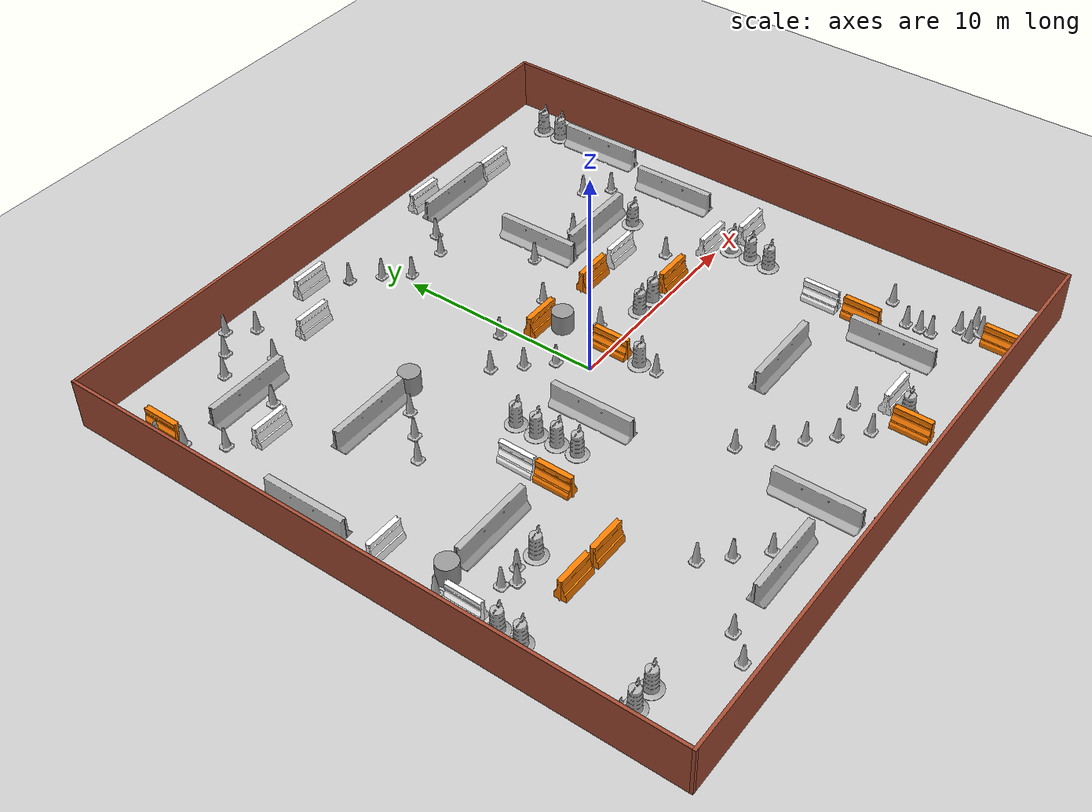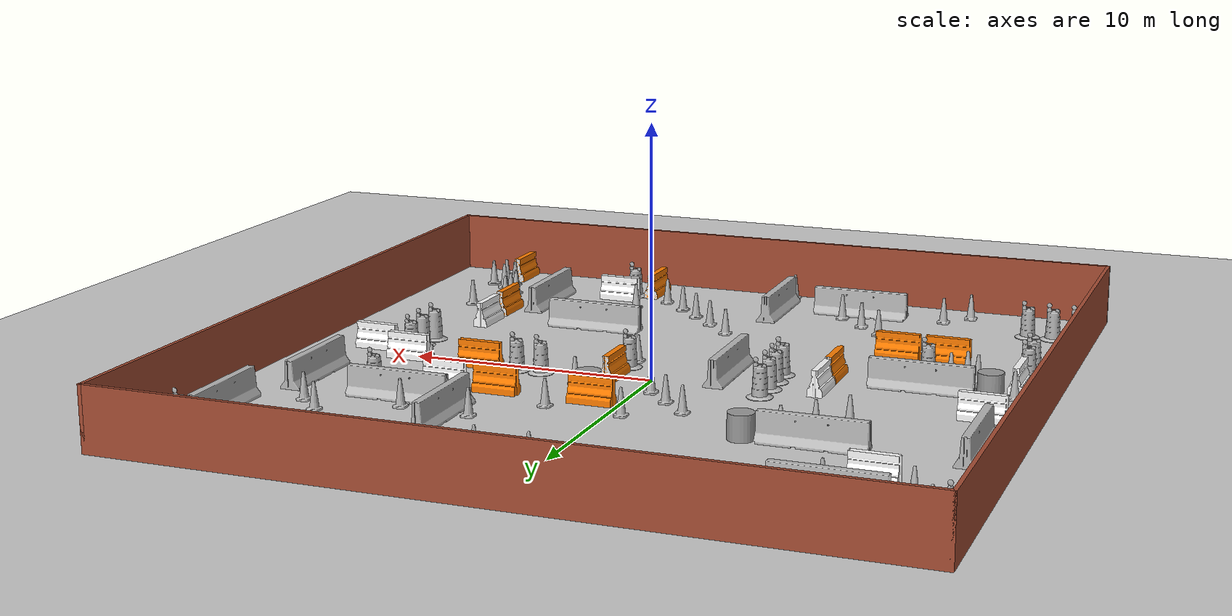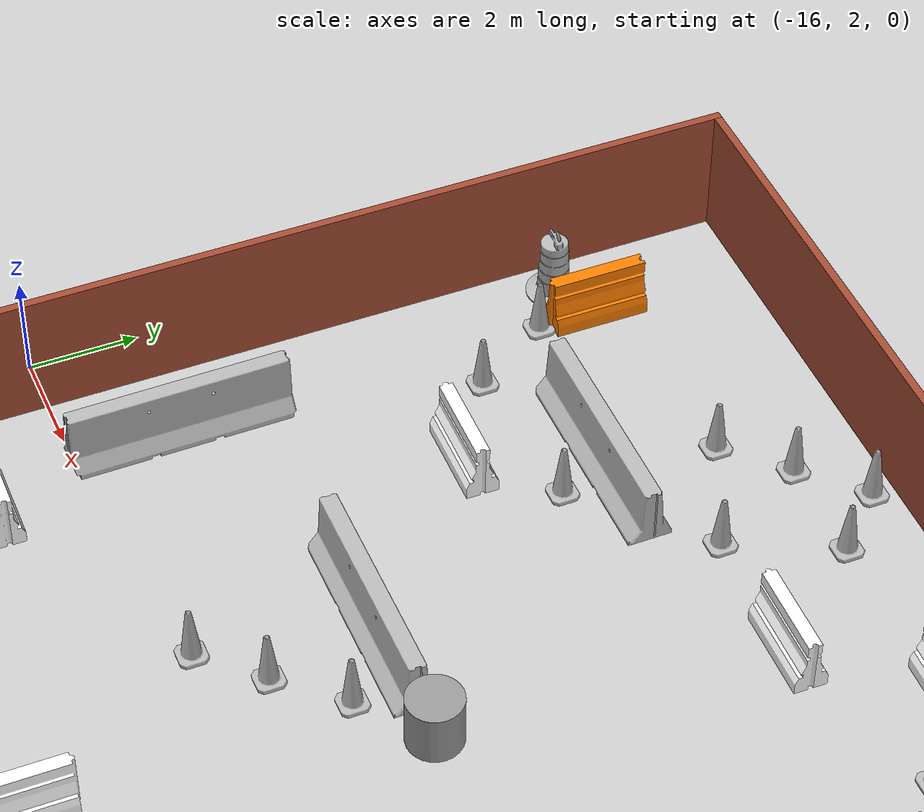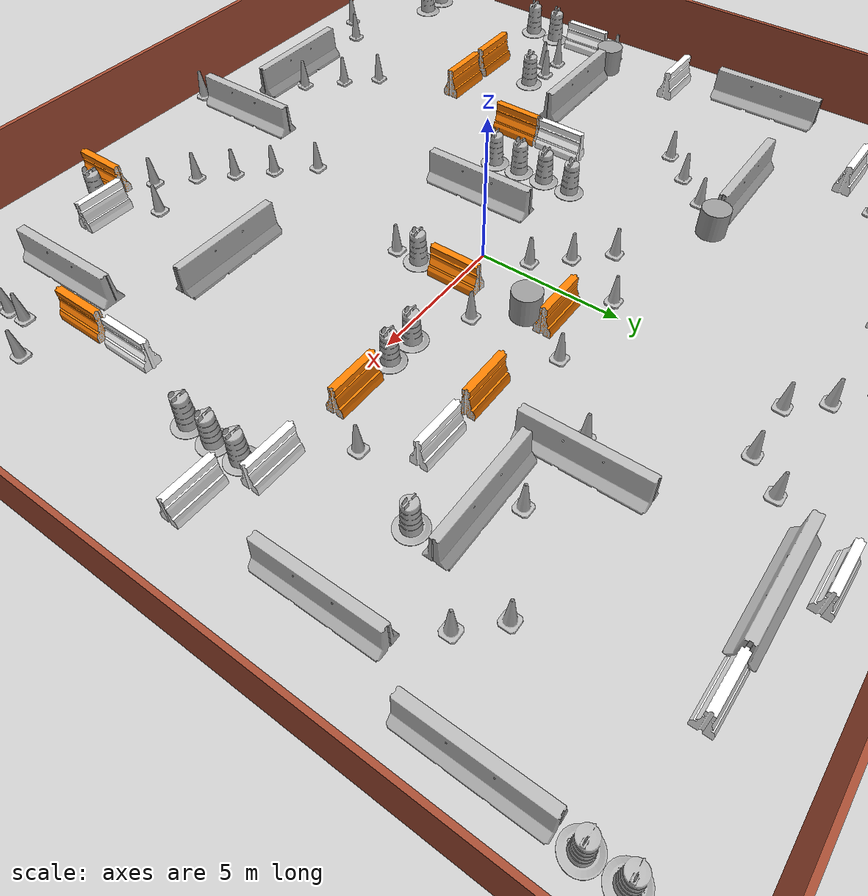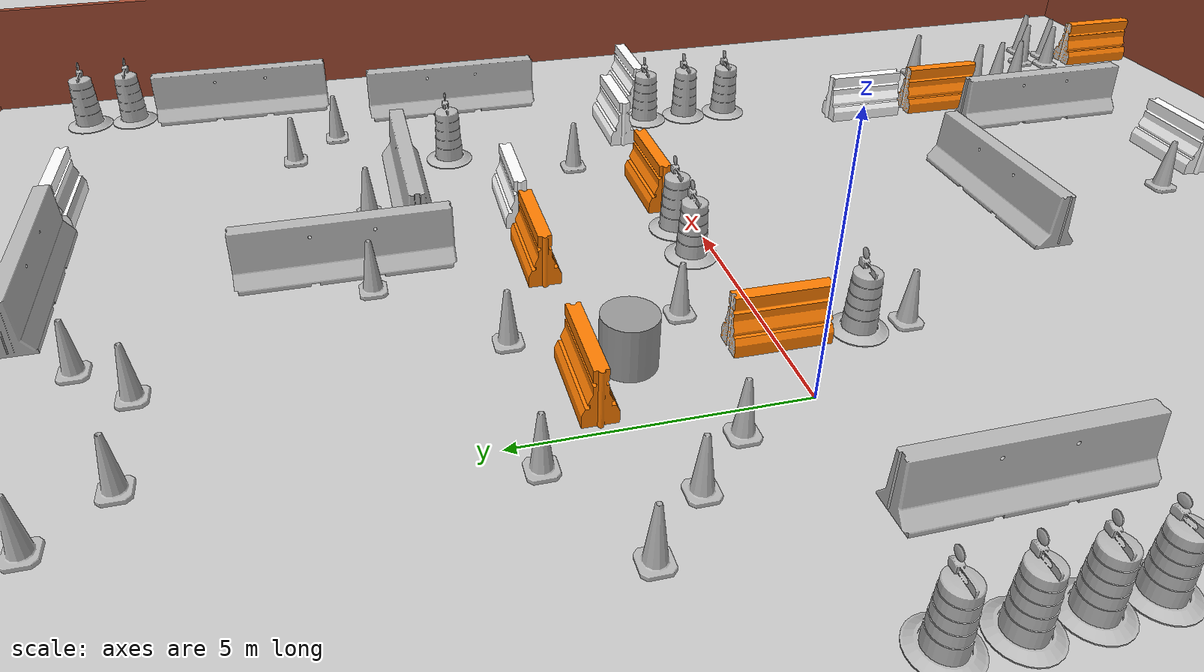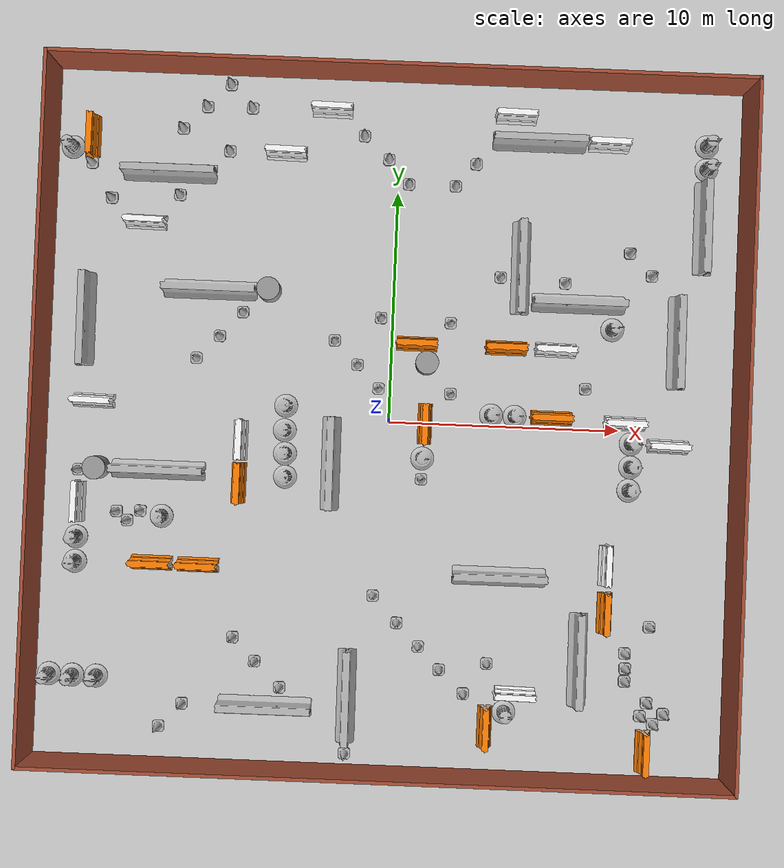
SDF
<sdf version="1.6">
 <world name="default">
  <light name="sun" type="directional">
   <pose>0 0 10 0 -0 0</pose>
   <diffuse>0.8 0.8 0.8 1</diffuse>
   <specular>0.2 0.2 0.2 1</specular>
   <attenuation>
    <range>1000</range>
    <constant>0.9</constant>
    <linear>0.01</linear>
    <quadratic>0.001</quadratic>
   </attenuation>
   <direction>-0.5 0.1 -0.9</direction>
  </light>
  <model name="ground_plane">
   <static>1</static>
   <link name="link">
    <collision name="collision">
     <geometry><plane><normal>0 0 1</normal><size>100 100</size></plane></geometry>
     <surface>
      <contact><collide_bitmask>65535</collide_bitmask></contact>
      <friction><ode><mu>100</mu><mu2>50</mu2></ode></friction>
     </surface>
    </collision>
    <visual name="visual">
     <cast_shadows>0</cast_shadows>
     <geometry><plane><normal>0 0 1</normal><size>100 100</size></plane></geometry>
     <material>
      <script><uri>file://media/materials/scripts/gazebo.material</uri><name>Gazebo/Grey</name></script>
     </material>
    </visual>
   </link>
  </model>
  <gravity>0 0 -9.8</gravity>
  <magnetic_field>6e-06 2.3e-05 -4.2e-05</magnetic_field>
  <atmosphere type="adiabatic"/>
  <physics name="default_physics" default="0" type="ode">
   <max_step_size>0.001</max_step_size>
   <real_time_factor>1</real_time_factor>
   <real_time_update_rate>1000</real_time_update_rate>
  </physics>
  <scene><ambient>0.4 0.4 0.4 1</ambient><background>0.7 0.7 0.7 1</background><shadows>1</shadows></scene>
  <spherical_coordinates>
   <surface_model>EARTH_WGS84</surface_model>
   <latitude_deg>0</latitude_deg>
   <longitude_deg>0</longitude_deg>
   <elevation>0</elevation>
   <heading_deg>0</heading_deg>
  </spherical_coordinates>
  <model name="30x30env"><static>0</static><pose>32.1206 3.39752 0 0 -0 0</pose></model>
  <model name="Construction Cone_0">
   <link name="link">
    <collision name="collision">
     <geometry>
      <mesh><scale>10 10 10</scale><uri>model://construction_cone/meshes/construction_cone.dae</uri></mesh>
     </geometry>
    </collision>
    <visual name="visual">
     <geometry>
      <mesh><scale>10 10 10</scale><uri>model://construction_cone/meshes/construction_cone.dae</uri></mesh>
     </geometry>
    </visual>
    <inertial>
     <inertia><ixx>1</ixx><ixy>0</ixy><ixz>0</ixz><iyy>1</iyy><iyz>0</iyz><izz>1</izz></inertia>
     <mass>1</mass>
    </inertial>
   </link>
   <pose>-7.48377 14.4957 -1e-05 -1e-06 0 0</pose>
  </model>
  <model name="Construction Cone_0_clone">
   <link name="link">
    <collision name="collision">
     <geometry>
      <mesh><scale>10 10 10</scale><uri>model://construction_cone/meshes/construction_cone.dae</uri></mesh>
     </geometry>
    </collision>
    <visual name="visual">
     <geometry>
      <mesh><scale>10 10 10</scale><uri>model://construction_cone/meshes/construction_cone.dae</uri></mesh>
     </geometry>
    </visual>
    <inertial>
     <inertia><ixx>1</ixx><ixy>0</ixy><ixz>0</ixz><iyy>1</iyy><iyz>0</iyz><izz>1</izz></inertia>
     <mass>1</mass>
    </inertial>
   </link>
   <pose>-8.4848 13.4919 -0 0 -0 0</pose>
  </model>
  <model name="Construction Cone_0_clone_1">
   <link name="link">
    <collision name="collision">
     <geometry>
      <mesh><scale>10 10 10</scale><uri>model://construction_cone/meshes/construction_cone.dae</uri></mesh>
     </geometry>
    </collision>
    <visual name="visual">
     <geometry>
      <mesh><scale>10 10 10</scale><uri>model://construction_cone/meshes/construction_cone.dae</uri></mesh>
     </geometry>
    </visual>
    <inertial>
     <inertia><ixx>1</ixx><ixy>0</ixy><ixz>0</ixz><iyy>1</iyy><iyz>0</iyz><izz>1</izz></inertia>
     <mass>1</mass>
    </inertial>
   </link>
   <pose>-6.51148 13.5032 -0 0 -0 0</pose>
  </model>
  <model name="drc_practice_white_jersey_barrier_clone">
   <static>1</static>
   <link name="link">
    <visual name="visual">
     <geometry>
      <mesh><uri>model://drc_practice_white_jersey_barrier/meshes/jersey_barrier.dae</uri></mesh>
     </geometry>
    </visual>
    <collision name="collision">
     <geometry>
      <mesh><uri>model://drc_practice_white_jersey_barrier/meshes/jersey_barrier.dae</uri></mesh>
     </geometry>
    </collision>
   </link>
   <pose>-2.98815 13.5359 0 0 0 -1.58176</pose>
  </model>
  <model name="drc_practice_white_jersey_barrier_clone_clone">
   <static>1</static>
   <link name="link">
    <visual name="visual">
     <geometry>
      <mesh><uri>model://drc_practice_white_jersey_barrier/meshes/jersey_barrier.dae</uri></mesh>
     </geometry>
    </visual>
    <collision name="collision">
     <geometry>
      <mesh><uri>model://drc_practice_white_jersey_barrier/meshes/jersey_barrier.dae</uri></mesh>
     </geometry>
    </collision>
   </link>
   <pose>-4.91611 11.5688 0 0 0 -1.58176</pose>
  </model>
  <model name="Construction Cone_0_clone_1_clone">
   <link name="link">
    <collision name="collision">
     <geometry>
      <mesh><scale>10 10 10</scale><uri>model://construction_cone/meshes/construction_cone.dae</uri></mesh>
     </geometry>
    </collision>
    <visual name="visual">
     <geometry>
      <mesh><scale>10 10 10</scale><uri>model://construction_cone/meshes/construction_cone.dae</uri></mesh>
     </geometry>
    </visual>
    <inertial>
     <inertia><ixx>1</ixx><ixy>0</ixy><ixz>0</ixz><iyy>1</iyy><iyz>0</iyz><izz>1</izz></inertia>
     <mass>1</mass>
    </inertial>
   </link>
   <pose>-1.56789 12.4756 -0 -0 -0 -0</pose>
  </model>
  <model name="Construction Cone_0_clone_1_clone_0">
   <link name="link">
    <collision name="collision">
     <geometry>
      <mesh><scale>10 10 10</scale><uri>model://construction_cone/meshes/construction_cone.dae</uri></mesh>
     </geometry>
    </collision>
    <visual name="visual">
     <geometry>
      <mesh><scale>10 10 10</scale><uri>model://construction_cone/meshes/construction_cone.dae</uri></mesh>
     </geometry>
    </visual>
    <inertial>
     <inertia><ixx>1</ixx><ixy>0</ixy><ixz>0</ixz><iyy>1</iyy><iyz>0</iyz><izz>1</izz></inertia>
     <mass>1</mass>
    </inertial>
   </link>
   <pose>-0.453751 11.482 -0 0 -0 0</pose>
  </model>
  <model name="Construction Cone_0_clone_1_clone_1">
   <link name="link">
    <collision name="collision">
     <geometry>
      <mesh><scale>10 10 10</scale><uri>model://construction_cone/meshes/construction_cone.dae</uri></mesh>
     </geometry>
    </collision>
    <visual name="visual">
     <geometry>
      <mesh><scale>10 10 10</scale><uri>model://construction_cone/meshes/construction_cone.dae</uri></mesh>
     </geometry>
    </visual>
    <inertial>
     <inertia><ixx>1</ixx><ixy>0</ixy><ixz>0</ixz><iyy>1</iyy><iyz>0</iyz><izz>1</izz></inertia>
     <mass>1</mass>
    </inertial>
   </link>
   <pose>0.453068 10.4369 -6e-06 2e-06 -0 0</pose>
  </model>
  <model name="Construction Cone_0_clone_1_clone_2">
   <link name="link">
    <collision name="collision">
     <geometry>
      <mesh><scale>10 10 10</scale><uri>model://construction_cone/meshes/construction_cone.dae</uri></mesh>
     </geometry>
    </collision>
    <visual name="visual">
     <geometry>
      <mesh><scale>10 10 10</scale><uri>model://construction_cone/meshes/construction_cone.dae</uri></mesh>
     </geometry>
    </visual>
    <inertial>
     <inertia><ixx>1</ixx><ixy>0</ixy><ixz>0</ixz><iyy>1</iyy><iyz>0</iyz><izz>1</izz></inertia>
     <mass>1</mass>
    </inertial>
   </link>
   <pose>2.49545 10.4343 -0 0 -0 0</pose>
  </model>
  <model name="Construction Cone_0_clone_1_clone_3">
   <link name="link">
    <collision name="collision">
     <geometry>
      <mesh><scale>10 10 10</scale><uri>model://construction_cone/meshes/construction_cone.dae</uri></mesh>
     </geometry>
    </collision>
    <visual name="visual">
     <geometry>
      <mesh><scale>10 10 10</scale><uri>model://construction_cone/meshes/construction_cone.dae</uri></mesh>
     </geometry>
    </visual>
    <inertial>
     <inertia><ixx>1</ixx><ixy>0</ixy><ixz>0</ixz><iyy>1</iyy><iyz>0</iyz><izz>1</izz></inertia>
     <mass>1</mass>
    </inertial>
   </link>
   <pose>3.36893 11.4327 -8e-06 1e-06 -0 0</pose>
  </model>
  <model name="jersey_barrier_clone">
   <static>1</static>
   <link name="link">
    <visual name="visual">
     <geometry><mesh><uri>model://jersey_barrier/meshes/jersey_barrier.dae</uri></mesh></geometry>
    </visual>
    <collision name="upright">
     <pose>0 0 0.5715 0 -0 0</pose>
     <geometry><box><size>4.06542 0.3063 1.143</size></box></geometry>
    </collision>
    <collision name="base">
     <pose>0 0 0.032258 0 -0 0</pose>
     <geometry><box><size>4.06542 0.8107 0.064516</size></box></geometry>
    </collision>
    <collision name="base2">
     <pose>0 0 0.1 0 -0 0</pose>
     <geometry><box><size>4.06542 0.65 0.1</size></box></geometry>
    </collision>
    <collision name="base3">
     <pose>0 0 0.2 0 -0 0</pose>
     <geometry><box><size>4.06542 0.5 0.1</size></box></geometry>
    </collision>
    <collision name="left-angle">
     <pose>0 -0.224 0.2401 0.9 -0 0</pose>
     <geometry><box><size>4.06542 0.5 0.064516</size></box></geometry>
    </collision>
    <collision name="right-angle">
     <pose>0 0.224 0.2401 -0.9 0 0</pose>
     <geometry><box><size>4.06542 0.5 0.064516</size></box></geometry>
    </collision>
   </link>
   <pose>6.07404 12.4971 0 0 -0 0</pose>
  </model>
  <model name="drc_practice_white_jersey_barrier_clone_clone_0">
   <static>1</static>
   <link name="link">
    <visual name="visual">
     <geometry>
      <mesh><uri>model://drc_practice_white_jersey_barrier/meshes/jersey_barrier.dae</uri></mesh>
     </geometry>
    </visual>
    <collision name="collision">
     <geometry>
      <mesh><uri>model://drc_practice_white_jersey_barrier/meshes/jersey_barrier.dae</uri></mesh>
     </geometry>
    </collision>
   </link>
   <pose>5.02744 13.5567 0 0 0 -1.58176</pose>
  </model>
  <model name="drc_practice_white_jersey_barrier_clone_clone_0_clone">
   <static>1</static>
   <link name="link">
    <visual name="visual">
     <geometry>
      <mesh><uri>model://drc_practice_white_jersey_barrier/meshes/jersey_barrier.dae</uri></mesh>
     </geometry>
    </visual>
    <collision name="collision">
     <geometry>
      <mesh><uri>model://drc_practice_white_jersey_barrier/meshes/jersey_barrier.dae</uri></mesh>
     </geometry>
    </collision>
   </link>
   <pose>9.10269 12.4765 0 0 0 -1.58176</pose>
  </model>
  <model name="Construction Cone_0_clone_0_clone">
   <link name="link">
    <collision name="collision">
     <geometry>
      <mesh><scale>10 10 10</scale><uri>model://construction_cone/meshes/construction_cone.dae</uri></mesh>
     </geometry>
    </collision>
    <visual name="visual">
     <geometry>
      <mesh><scale>10 10 10</scale><uri>model://construction_cone/meshes/construction_cone.dae</uri></mesh>
     </geometry>
    </visual>
    <inertial>
     <inertia><ixx>1</ixx><ixy>0</ixy><ixz>0</ixz><iyy>1</iyy><iyz>0</iyz><izz>1</izz></inertia>
     <mass>1</mass>
    </inertial>
   </link>
   <pose>-12.5113 9.33697 -0 0 -1e-06 0</pose>
  </model>
  <model name="jersey_barrier_clone_clone">
   <static>1</static>
   <link name="link">
    <visual name="visual">
     <geometry><mesh><uri>model://jersey_barrier/meshes/jersey_barrier.dae</uri></mesh></geometry>
    </visual>
    <collision name="upright">
     <pose>0 0 0.5715 0 -0 0</pose>
     <geometry><box><size>4.06542 0.3063 1.143</size></box></geometry>
    </collision>
    <collision name="base">
     <pose>0 0 0.032258 0 -0 0</pose>
     <geometry><box><size>4.06542 0.8107 0.064516</size></box></geometry>
    </collision>
    <collision name="base2">
     <pose>0 0 0.1 0 -0 0</pose>
     <geometry><box><size>4.06542 0.65 0.1</size></box></geometry>
    </collision>
    <collision name="base3">
     <pose>0 0 0.2 0 -0 0</pose>
     <geometry><box><size>4.06542 0.5 0.1</size></box></geometry>
    </collision>
    <collision name="left-angle">
     <pose>0 -0.224 0.2401 0.9 -0 0</pose>
     <geometry><box><size>4.06542 0.5 0.064516</size></box></geometry>
    </collision>
    <collision name="right-angle">
     <pose>0 0.224 0.2401 -0.9 0 0</pose>
     <geometry><box><size>4.06542 0.5 0.064516</size></box></geometry>
    </collision>
   </link>
   <pose>-9.9787 10.5294 0 0 -0 0</pose>
  </model>
  <model name="Construction Cone_0_clone_0_clone_clone">
   <link name="link">
    <collision name="collision">
     <geometry>
      <mesh><scale>10 10 10</scale><uri>model://construction_cone/meshes/construction_cone.dae</uri></mesh>
     </geometry>
    </collision>
    <visual name="visual">
     <geometry>
      <mesh><scale>10 10 10</scale><uri>model://construction_cone/meshes/construction_cone.dae</uri></mesh>
     </geometry>
    </visual>
    <inertial>
     <inertia><ixx>1</ixx><ixy>0</ixy><ixz>0</ixz><iyy>1</iyy><iyz>0</iyz><izz>1</izz></inertia>
     <mass>1</mass>
    </inertial>
   </link>
   <pose>-9.53841 9.57947 -0 0 -1e-06 0</pose>
  </model>
  <model name="drc_practice_white_jersey_barrier_clone_clone_clone">
   <static>1</static>
   <link name="link">
    <visual name="visual">
     <geometry>
      <mesh><uri>model://drc_practice_white_jersey_barrier/meshes/jersey_barrier.dae</uri></mesh>
     </geometry>
    </visual>
    <collision name="collision">
     <geometry>
      <mesh><uri>model://drc_practice_white_jersey_barrier/meshes/jersey_barrier.dae</uri></mesh>
     </geometry>
    </collision>
   </link>
   <pose>-10.924 8.31727 0 0 0 -1.58176</pose>
  </model>
  <model name="Construction Cone_0_clone_0_clone_clone_clone">
   <link name="link">
    <collision name="collision">
     <geometry>
      <mesh><scale>10 10 10</scale><uri>model://construction_cone/meshes/construction_cone.dae</uri></mesh>
     </geometry>
    </collision>
    <visual name="visual">
     <geometry>
      <mesh><scale>10 10 10</scale><uri>model://construction_cone/meshes/construction_cone.dae</uri></mesh>
     </geometry>
    </visual>
    <inertial>
     <inertia><ixx>1</ixx><ixy>0</ixy><ixz>0</ixz><iyy>1</iyy><iyz>0</iyz><izz>1</izz></inertia>
     <mass>1</mass>
    </inertial>
   </link>
   <pose>-7.42849 11.576 -0 0 -0 0</pose>
  </model>
  <model name="jersey_barrier_clone_clone_clone">
   <static>1</static>
   <link name="link">
    <visual name="visual">
     <geometry><mesh><uri>model://jersey_barrier/meshes/jersey_barrier.dae</uri></mesh></geometry>
    </visual>
    <collision name="upright">
     <pose>0 0 0.5715 0 -0 0</pose>
     <geometry><box><size>4.06542 0.3063 1.143</size></box></geometry>
    </collision>
    <collision name="base">
     <pose>0 0 0.032258 0 -0 0</pose>
     <geometry><box><size>4.06542 0.8107 0.064516</size></box></geometry>
    </collision>
    <collision name="base2">
     <pose>0 0 0.1 0 -0 0</pose>
     <geometry><box><size>4.06542 0.65 0.1</size></box></geometry>
    </collision>
    <collision name="base3">
     <pose>0 0 0.2 0 -0 0</pose>
     <geometry><box><size>4.06542 0.5 0.1</size></box></geometry>
    </collision>
    <collision name="left-angle">
     <pose>0 -0.224 0.2401 0.9 -0 0</pose>
     <geometry><box><size>4.06542 0.5 0.064516</size></box></geometry>
    </collision>
    <collision name="right-angle">
     <pose>0 0.224 0.2401 -0.9 0 0</pose>
     <geometry><box><size>4.06542 0.5 0.064516</size></box></geometry>
    </collision>
   </link>
   <pose>-13.4245 3.97341 0 0 0 -1.56391</pose>
  </model>
  <model name="drc_practice_white_jersey_barrier_clone_clone_clone_clone">
   <static>1</static>
   <link name="link">
    <visual name="visual">
     <geometry>
      <mesh><uri>model://drc_practice_white_jersey_barrier/meshes/jersey_barrier.dae</uri></mesh>
     </geometry>
    </visual>
    <collision name="collision">
     <geometry>
      <mesh><uri>model://drc_practice_white_jersey_barrier/meshes/jersey_barrier.dae</uri></mesh>
     </geometry>
    </collision>
   </link>
   <pose>-12.8698 0.433734 0 0 0 -1.58176</pose>
  </model>
  <model name="jersey_barrier_clone_clone_clone_0">
   <static>1</static>
   <link name="link">
    <visual name="visual">
     <geometry><mesh><uri>model://jersey_barrier/meshes/jersey_barrier.dae</uri></mesh></geometry>
    </visual>
    <collision name="upright">
     <pose>0 0 0.5715 0 -0 0</pose>
     <geometry><box><size>4.06542 0.3063 1.143</size></box></geometry>
    </collision>
    <collision name="base">
     <pose>0 0 0.032258 0 -0 0</pose>
     <geometry><box><size>4.06542 0.8107 0.064516</size></box></geometry>
    </collision>
    <collision name="base2">
     <pose>0 0 0.1 0 -0 0</pose>
     <geometry><box><size>4.06542 0.65 0.1</size></box></geometry>
    </collision>
    <collision name="base3">
     <pose>0 0 0.2 0 -0 0</pose>
     <geometry><box><size>4.06542 0.5 0.1</size></box></geometry>
    </collision>
    <collision name="left-angle">
     <pose>0 -0.224 0.2401 0.9 -0 0</pose>
     <geometry><box><size>4.06542 0.5 0.064516</size></box></geometry>
    </collision>
    <collision name="right-angle">
     <pose>0 0.224 0.2401 -0.9 0 0</pose>
     <geometry><box><size>4.06542 0.5 0.064516</size></box></geometry>
    </collision>
   </link>
   <pose>-8.01638 5.47012 0 0 -0 0</pose>
  </model>
  <model name="unit_cylinder">
   <pose>-5.42848 5.52156 0.499997 1e-06 -0 0</pose>
   <link name="link">
    <inertial>
     <mass>1</mass>
     <inertia><ixx>0.145833</ixx><ixy>0</ixy><ixz>0</ixz><iyy>0.145833</iyy><iyz>0</iyz><izz>0.125</izz></inertia>
    </inertial>
    <collision name="collision">
     <geometry><cylinder><radius>0.5</radius><length>1</length></cylinder></geometry>
    </collision>
    <visual name="visual">
     <geometry><cylinder><radius>0.5</radius><length>1</length></cylinder></geometry>
     <material>
      <script><name>Gazebo/Grey</name><uri>file://media/materials/scripts/gazebo.material</uri></script>
     </material>
    </visual>
   </link>
  </model>
  <model name="Construction Cone_0_clone_0_clone_clone_0">
   <link name="link">
    <collision name="collision">
     <geometry>
      <mesh><scale>10 10 10</scale><uri>model://construction_cone/meshes/construction_cone.dae</uri></mesh>
     </geometry>
    </collision>
    <visual name="visual">
     <geometry>
      <mesh><scale>10 10 10</scale><uri>model://construction_cone/meshes/construction_cone.dae</uri></mesh>
     </geometry>
    </visual>
    <inertial>
     <inertia><ixx>1</ixx><ixy>0</ixy><ixz>0</ixz><iyy>1</iyy><iyz>0</iyz><izz>1</izz></inertia>
     <mass>1</mass>
    </inertial>
   </link>
   <pose>-6.57528 4.55392 -1e-05 -1e-06 -0 -0</pose>
  </model>
  <model name="Construction Cone_0_clone_0_clone_clone_1">
   <link name="link">
    <collision name="collision">
     <geometry>
      <mesh><scale>10 10 10</scale><uri>model://construction_cone/meshes/construction_cone.dae</uri></mesh>
     </geometry>
    </collision>
    <visual name="visual">
     <geometry>
      <mesh><scale>10 10 10</scale><uri>model://construction_cone/meshes/construction_cone.dae</uri></mesh>
     </geometry>
    </visual>
    <inertial>
     <inertia><ixx>1</ixx><ixy>0</ixy><ixz>0</ixz><iyy>1</iyy><iyz>0</iyz><izz>1</izz></inertia>
     <mass>1</mass>
    </inertial>
   </link>
   <pose>-7.55022 3.47181 -0 0 -1e-06 0</pose>
  </model>
  <model name="Construction Cone_0_clone_0_clone_clone_2">
   <link name="link">
    <collision name="collision">
     <geometry>
      <mesh><scale>10 10 10</scale><uri>model://construction_cone/meshes/construction_cone.dae</uri></mesh>
     </geometry>
    </collision>
    <visual name="visual">
     <geometry>
      <mesh><scale>10 10 10</scale><uri>model://construction_cone/meshes/construction_cone.dae</uri></mesh>
     </geometry>
    </visual>
    <inertial>
     <inertia><ixx>1</ixx><ixy>0</ixy><ixz>0</ixz><iyy>1</iyy><iyz>0</iyz><izz>1</izz></inertia>
     <mass>1</mass>
    </inertial>
   </link>
   <pose>-8.52384 2.47533 -0 0 -1e-06 0</pose>
  </model>
  <model name="Construction Cone_0_clone_1_clone_1_clone">
   <link name="link">
    <collision name="collision">
     <geometry>
      <mesh><scale>10 10 10</scale><uri>model://construction_cone/meshes/construction_cone.dae</uri></mesh>
     </geometry>
    </collision>
    <visual name="visual">
     <geometry>
      <mesh><scale>10 10 10</scale><uri>model://construction_cone/meshes/construction_cone.dae</uri></mesh>
     </geometry>
    </visual>
    <inertial>
     <inertia><ixx>1</ixx><ixy>0</ixy><ixz>0</ixz><iyy>1</iyy><iyz>0</iyz><izz>1</izz></inertia>
     <mass>1</mass>
    </inertial>
   </link>
   <pose>-2.52061 3.47667 -4e-06 4e-06 -1e-06 0</pose>
  </model>
  <model name="Construction Cone_0_clone_1_clone_1_clone_0">
   <link name="link">
    <collision name="collision">
     <geometry>
      <mesh><scale>10 10 10</scale><uri>model://construction_cone/meshes/construction_cone.dae</uri></mesh>
     </geometry>
    </collision>
    <visual name="visual">
     <geometry>
      <mesh><scale>10 10 10</scale><uri>model://construction_cone/meshes/construction_cone.dae</uri></mesh>
     </geometry>
    </visual>
    <inertial>
     <inertia><ixx>1</ixx><ixy>0</ixy><ixz>0</ixz><iyy>1</iyy><iyz>0</iyz><izz>1</izz></inertia>
     <mass>1</mass>
    </inertial>
   </link>
   <pose>-1.49053 2.45106 -0 0 -0 0</pose>
  </model>
  <model name="Construction Cone_0_clone_1_clone_1_clone_1">
   <link name="link">
    <collision name="collision">
     <geometry>
      <mesh><scale>10 10 10</scale><uri>model://construction_cone/meshes/construction_cone.dae</uri></mesh>
     </geometry>
    </collision>
    <visual name="visual">
     <geometry>
      <mesh><scale>10 10 10</scale><uri>model://construction_cone/meshes/construction_cone.dae</uri></mesh>
     </geometry>
    </visual>
    <inertial>
     <inertia><ixx>1</ixx><ixy>0</ixy><ixz>0</ixz><iyy>1</iyy><iyz>0</iyz><izz>1</izz></inertia>
     <mass>1</mass>
    </inertial>
   </link>
   <pose>-0.52873 1.44362 -1e-05 -1e-06 0 0</pose>
  </model>
  <model name="drc_practice_organge_jersey_barrier_clone_clone">
   <static>1</static>
   <link name="link">
    <visual name="visual">
     <geometry>
      <mesh><uri>model://drc_practice_orange_jersey_barrier/meshes/jersey_barrier.dae</uri></mesh>
     </geometry>
    </visual>
    <collision name="collision">
     <geometry>
      <mesh><uri>model://drc_practice_orange_jersey_barrier/meshes/jersey_barrier.dae</uri></mesh>
     </geometry>
    </collision>
   </link>
   <pose>1.07469 3.45393 0 0 0 -1.56865</pose>
  </model>
  <model name="Construction Cone_0_clone_1_clone_1_clone_clone">
   <link name="link">
    <collision name="collision">
     <geometry>
      <mesh><scale>10 10 10</scale><uri>model://construction_cone/meshes/construction_cone.dae</uri></mesh>
     </geometry>
    </collision>
    <visual name="visual">
     <geometry>
      <mesh><scale>10 10 10</scale><uri>model://construction_cone/meshes/construction_cone.dae</uri></mesh>
     </geometry>
    </visual>
    <inertial>
     <inertia><ixx>1</ixx><ixy>0</ixy><ixz>0</ixz><iyy>1</iyy><iyz>0</iyz><izz>1</izz></inertia>
     <mass>1</mass>
    </inertial>
   </link>
   <pose>-0.534948 4.5351 -0 0 -1e-06 0</pose>
  </model>
  <model name="Construction Cone_0_clone_1_clone_1_clone_clone_0">
   <link name="link">
    <collision name="collision">
     <geometry>
      <mesh><scale>10 10 10</scale><uri>model://construction_cone/meshes/construction_cone.dae</uri></mesh>
     </geometry>
    </collision>
    <visual name="visual">
     <geometry>
      <mesh><scale>10 10 10</scale><uri>model://construction_cone/meshes/construction_cone.dae</uri></mesh>
     </geometry>
    </visual>
    <inertial>
     <inertia><ixx>1</ixx><ixy>0</ixy><ixz>0</ixz><iyy>1</iyy><iyz>0</iyz><izz>1</izz></inertia>
     <mass>1</mass>
    </inertial>
   </link>
   <pose>2.51012 4.42717 -0 0 -1e-06 0</pose>
  </model>
  <model name="unit_cylinder_clone">
   <pose>1.53143 2.61052 0.499994 -1e-06 -0 -0</pose>
   <link name="link">
    <inertial>
     <mass>1</mass>
     <inertia><ixx>0.145833</ixx><ixy>0</ixy><ixz>0</ixz><iyy>0.145833</iyy><iyz>0</iyz><izz>0.125</izz></inertia>
    </inertial>
    <collision name="collision">
     <geometry><cylinder><radius>0.5</radius><length>1</length></cylinder></geometry>
    </collision>
    <visual name="visual">
     <geometry><cylinder><radius>0.5</radius><length>1</length></cylinder></geometry>
     <material>
      <script><name>Gazebo/Grey</name><uri>file://media/materials/scripts/gazebo.material</uri></script>
     </material>
    </visual>
   </link>
  </model>
  <model name="Construction Cone_0_clone_1_clone_1_clone_clone_clone">
   <link name="link">
    <collision name="collision">
     <geometry>
      <mesh><scale>10 10 10</scale><uri>model://construction_cone/meshes/construction_cone.dae</uri></mesh>
     </geometry>
    </collision>
    <visual name="visual">
     <geometry>
      <mesh><scale>10 10 10</scale><uri>model://construction_cone/meshes/construction_cone.dae</uri></mesh>
     </geometry>
    </visual>
    <inertial>
     <inertia><ixx>1</ixx><ixy>0</ixy><ixz>0</ixz><iyy>1</iyy><iyz>0</iyz><izz>1</izz></inertia>
     <mass>1</mass>
    </inertial>
   </link>
   <pose>2.61559 1.33957 -0 0 -0 0</pose>
  </model>
  <model name="jersey_barrier_clone_clone_clone_clone">
   <static>1</static>
   <link name="link">
    <visual name="visual">
     <geometry><mesh><uri>model://jersey_barrier/meshes/jersey_barrier.dae</uri></mesh></geometry>
    </visual>
    <collision name="upright">
     <pose>0 0 0.5715 0 -0 0</pose>
     <geometry><box><size>4.06542 0.3063 1.143</size></box></geometry>
    </collision>
    <collision name="base">
     <pose>0 0 0.032258 0 -0 0</pose>
     <geometry><box><size>4.06542 0.8107 0.064516</size></box></geometry>
    </collision>
    <collision name="base2">
     <pose>0 0 0.1 0 -0 0</pose>
     <geometry><box><size>4.06542 0.65 0.1</size></box></geometry>
    </collision>
    <collision name="base3">
     <pose>0 0 0.2 0 -0 0</pose>
     <geometry><box><size>4.06542 0.5 0.1</size></box></geometry>
    </collision>
    <collision name="left-angle">
     <pose>0 -0.224 0.2401 0.9 -0 0</pose>
     <geometry><box><size>4.06542 0.5 0.064516</size></box></geometry>
    </collision>
    <collision name="right-angle">
     <pose>0 0.224 0.2401 -0.9 0 0</pose>
     <geometry><box><size>4.06542 0.5 0.064516</size></box></geometry>
    </collision>
   </link>
   <pose>5.4717 6.94023 0 0 0 -1.56391</pose>
  </model>
  <model name="Construction Cone_0_clone_1_clone_1_clone_clone_0_clone">
   <link name="link">
    <collision name="collision">
     <geometry>
      <mesh><scale>10 10 10</scale><uri>model://construction_cone/meshes/construction_cone.dae</uri></mesh>
     </geometry>
    </collision>
    <visual name="visual">
     <geometry>
      <mesh><scale>10 10 10</scale><uri>model://construction_cone/meshes/construction_cone.dae</uri></mesh>
     </geometry>
    </visual>
    <inertial>
     <inertia><ixx>1</ixx><ixy>0</ixy><ixz>0</ixz><iyy>1</iyy><iyz>0</iyz><izz>1</izz></inertia>
     <mass>1</mass>
    </inertial>
   </link>
   <pose>4.6175 6.51869 -6e-06 -4e-06 0 0</pose>
  </model>
  <model name="jersey_barrier_clone_clone_0">
   <static>1</static>
   <link name="link">
    <visual name="visual">
     <geometry><mesh><uri>model://jersey_barrier/meshes/jersey_barrier.dae</uri></mesh></geometry>
    </visual>
    <collision name="upright">
     <pose>0 0 0.5715 0 -0 0</pose>
     <geometry><box><size>4.06542 0.3063 1.143</size></box></geometry>
    </collision>
    <collision name="base">
     <pose>0 0 0.032258 0 -0 0</pose>
     <geometry><box><size>4.06542 0.8107 0.064516</size></box></geometry>
    </collision>
    <collision name="base2">
     <pose>0 0 0.1 0 -0 0</pose>
     <geometry><box><size>4.06542 0.65 0.1</size></box></geometry>
    </collision>
    <collision name="base3">
     <pose>0 0 0.2 0 -0 0</pose>
     <geometry><box><size>4.06542 0.5 0.1</size></box></geometry>
    </collision>
    <collision name="left-angle">
     <pose>0 -0.224 0.2401 0.9 -0 0</pose>
     <geometry><box><size>4.06542 0.5 0.064516</size></box></geometry>
    </collision>
    <collision name="right-angle">
     <pose>0 0.224 0.2401 -0.9 0 0</pose>
     <geometry><box><size>4.06542 0.5 0.064516</size></box></geometry>
    </collision>
   </link>
   <pose>8.03198 5.48004 0 0 -0 0</pose>
  </model>
  <model name="Construction Cone_0_clone_1_clone_1_clone_clone_0_clone_0">
   <link name="link">
    <collision name="collision">
     <geometry>
      <mesh><scale>10 10 10</scale><uri>model://construction_cone/meshes/construction_cone.dae</uri></mesh>
     </geometry>
    </collision>
    <visual name="visual">
     <geometry>
      <mesh><scale>10 10 10</scale><uri>model://construction_cone/meshes/construction_cone.dae</uri></mesh>
     </geometry>
    </visual>
    <inertial>
     <inertia><ixx>1</ixx><ixy>0</ixy><ixz>0</ixz><iyy>1</iyy><iyz>0</iyz><izz>1</izz></inertia>
     <mass>1</mass>
    </inertial>
   </link>
   <pose>7.45326 6.3667 -0 0 -0 0</pose>
  </model>
  <model name="Construction Barrel_clone_clone_clone">
   <link name="link">
    <inertial>
     <pose>0 0 0.4 0 -0 0</pose>
     <mass>500</mass>
     <inertia><ixx>51.2096</ixx><iyy>51.2096</iyy><izz>25</izz><ixy>0</ixy><ixz>0</ixz><iyz>0</iyz></inertia>
    </inertial>
    <collision name="collision">
     <geometry><mesh><uri>model://construction_barrel/meshes/construction_barrel.dae</uri></mesh></geometry>
    </collision>
    <visual name="visual">
     <geometry><mesh><uri>model://construction_barrel/meshes/construction_barrel.dae</uri></mesh></geometry>
    </visual>
   </link>
   <pose>9.58015 4.40789 0 0 0 -0.000522</pose>
  </model>
  <model name="jersey_barrier_clone_clone_clone_clone_clone">
   <static>1</static>
   <link name="link">
    <visual name="visual">
     <geometry><mesh><uri>model://jersey_barrier/meshes/jersey_barrier.dae</uri></mesh></geometry>
    </visual>
    <collision name="upright">
     <pose>0 0 0.5715 0 -0 0</pose>
     <geometry><box><size>4.06542 0.3063 1.143</size></box></geometry>
    </collision>
    <collision name="base">
     <pose>0 0 0.032258 0 -0 0</pose>
     <geometry><box><size>4.06542 0.8107 0.064516</size></box></geometry>
    </collision>
    <collision name="base2">
     <pose>0 0 0.1 0 -0 0</pose>
     <geometry><box><size>4.06542 0.65 0.1</size></box></geometry>
    </collision>
    <collision name="base3">
     <pose>0 0 0.2 0 -0 0</pose>
     <geometry><box><size>4.06542 0.5 0.1</size></box></geometry>
    </collision>
    <collision name="left-angle">
     <pose>0 -0.224 0.2401 0.9 -0 0</pose>
     <geometry><box><size>4.06542 0.5 0.064516</size></box></geometry>
    </collision>
    <collision name="right-angle">
     <pose>0 0.224 0.2401 -0.9 0 0</pose>
     <geometry><box><size>4.06542 0.5 0.064516</size></box></geometry>
    </collision>
   </link>
   <pose>13.3725 8.96891 0 0 0 -1.56391</pose>
  </model>
  <model name="Construction Barrel_clone_clone_clone_clone">
   <link name="link">
    <inertial>
     <pose>0 0 0.4 0 -0 0</pose>
     <mass>500</mass>
     <inertia><ixx>51.2096</ixx><iyy>51.2096</iyy><izz>25</izz><ixy>0</ixy><ixz>0</ixz><iyz>0</iyz></inertia>
    </inertial>
    <collision name="collision">
     <geometry><mesh><uri>model://construction_barrel/meshes/construction_barrel.dae</uri></mesh></geometry>
    </collision>
    <visual name="visual">
     <geometry><mesh><uri>model://construction_barrel/meshes/construction_barrel.dae</uri></mesh></geometry>
    </visual>
   </link>
   <pose>13.4236 12.6037 -0 1e-06 -1e-06 0.032681</pose>
  </model>
  <model name="Construction Barrel_clone_clone_clone_clone_0">
   <link name="link">
    <inertial>
     <pose>0 0 0.4 0 -0 0</pose>
     <mass>500</mass>
     <inertia><ixx>51.2096</ixx><iyy>51.2096</iyy><izz>25</izz><ixy>0</ixy><ixz>0</ixz><iyz>0</iyz></inertia>
    </inertial>
    <collision name="collision">
     <geometry><mesh><uri>model://construction_barrel/meshes/construction_barrel.dae</uri></mesh></geometry>
    </collision>
    <visual name="visual">
     <geometry><mesh><uri>model://construction_barrel/meshes/construction_barrel.dae</uri></mesh></geometry>
    </visual>
   </link>
   <pose>13.4407 11.5814 -1e-06 2e-06 -2e-06 -0.01261</pose>
  </model>
  <model name="jersey_barrier_clone_clone_clone_clone_clone_clone">
   <static>1</static>
   <link name="link">
    <visual name="visual">
     <geometry><mesh><uri>model://jersey_barrier/meshes/jersey_barrier.dae</uri></mesh></geometry>
    </visual>
    <collision name="upright">
     <pose>0 0 0.5715 0 -0 0</pose>
     <geometry><box><size>4.06542 0.3063 1.143</size></box></geometry>
    </collision>
    <collision name="base">
     <pose>0 0 0.032258 0 -0 0</pose>
     <geometry><box><size>4.06542 0.8107 0.064516</size></box></geometry>
    </collision>
    <collision name="base2">
     <pose>0 0 0.1 0 -0 0</pose>
     <geometry><box><size>4.06542 0.65 0.1</size></box></geometry>
    </collision>
    <collision name="base3">
     <pose>0 0 0.2 0 -0 0</pose>
     <geometry><box><size>4.06542 0.5 0.1</size></box></geometry>
    </collision>
    <collision name="left-angle">
     <pose>0 -0.224 0.2401 0.9 -0 0</pose>
     <geometry><box><size>4.06542 0.5 0.064516</size></box></geometry>
    </collision>
    <collision name="right-angle">
     <pose>0 0.224 0.2401 -0.9 0 0</pose>
     <geometry><box><size>4.06542 0.5 0.064516</size></box></geometry>
    </collision>
   </link>
   <pose>12.4106 3.92831 0 0 0 -1.56391</pose>
  </model>
  <model name="drc_practice_organge_jersey_barrier_clone_clone_clone">
   <static>1</static>
   <link name="link">
    <visual name="visual">
     <geometry>
      <mesh><uri>model://drc_practice_orange_jersey_barrier/meshes/jersey_barrier.dae</uri></mesh>
     </geometry>
    </visual>
    <collision name="collision">
     <geometry>
      <mesh><uri>model://drc_practice_orange_jersey_barrier/meshes/jersey_barrier.dae</uri></mesh>
     </geometry>
    </collision>
   </link>
   <pose>4.96339 3.42606 0 0 0 -1.56865</pose>
  </model>
  <model name="drc_practice_white_jersey_barrier_clone_clone_0_clone_clone">
   <static>1</static>
   <link name="link">
    <visual name="visual">
     <geometry>
      <mesh><uri>model://drc_practice_white_jersey_barrier/meshes/jersey_barrier.dae</uri></mesh>
     </geometry>
    </visual>
    <collision name="collision">
     <geometry>
      <mesh><uri>model://drc_practice_white_jersey_barrier/meshes/jersey_barrier.dae</uri></mesh>
     </geometry>
    </collision>
   </link>
   <pose>7.11317 3.42217 0 0 0 -1.58176</pose>
  </model>
  <model name="Construction Barrel_clone_clone_0">
   <link name="link">
    <inertial>
     <pose>0 0 0.4 0 -0 0</pose>
     <mass>500</mass>
     <inertia><ixx>51.2096</ixx><iyy>51.2096</iyy><izz>25</izz><ixy>0</ixy><ixz>0</ixz><iyz>0</iyz></inertia>
    </inertial>
    <collision name="collision">
     <geometry><mesh><uri>model://construction_barrel/meshes/construction_barrel.dae</uri></mesh></geometry>
    </collision>
    <visual name="visual">
     <geometry><mesh><uri>model://construction_barrel/meshes/construction_barrel.dae</uri></mesh></geometry>
    </visual>
   </link>
   <pose>-4.52804 0.534334 -1e-06 2e-06 -2e-06 -0.000529</pose>
  </model>
  <model name="Construction Barrel_clone_clone_0_clone">
   <link name="link">
    <inertial>
     <pose>0 0 0.4 0 -0 0</pose>
     <mass>500</mass>
     <inertia><ixx>51.2096</ixx><iyy>51.2096</iyy><izz>25</izz><ixy>0</ixy><ixz>0</ixz><iyz>0</iyz></inertia>
    </inertial>
    <collision name="collision">
     <geometry><mesh><uri>model://construction_barrel/meshes/construction_barrel.dae</uri></mesh></geometry>
    </collision>
    <visual name="visual">
     <geometry><mesh><uri>model://construction_barrel/meshes/construction_barrel.dae</uri></mesh></geometry>
    </visual>
   </link>
   <pose>-4.54616 -0.53028 0 0 0 -0.000533</pose>
  </model>
  <model name="Construction Barrel_clone_clone_0_clone_0">
   <link name="link">
    <inertial>
     <pose>0 0 0.4 0 -0 0</pose>
     <mass>500</mass>
     <inertia><ixx>51.2096</ixx><iyy>51.2096</iyy><izz>25</izz><ixy>0</ixy><ixz>0</ixz><iyz>0</iyz></inertia>
    </inertial>
    <collision name="collision">
     <geometry><mesh><uri>model://construction_barrel/meshes/construction_barrel.dae</uri></mesh></geometry>
    </collision>
    <visual name="visual">
     <geometry><mesh><uri>model://construction_barrel/meshes/construction_barrel.dae</uri></mesh></geometry>
    </visual>
   </link>
   <pose>-4.49561 -1.55108 0 0 0 -0.104562</pose>
  </model>
  <model name="Construction Barrel_clone_clone_0_clone_1">
   <link name="link">
    <inertial>
     <pose>0 0 0.4 0 -0 0</pose>
     <mass>500</mass>
     <inertia><ixx>51.2096</ixx><iyy>51.2096</iyy><izz>25</izz><ixy>0</ixy><ixz>0</ixz><iyz>0</iyz></inertia>
    </inertial>
    <collision name="collision">
     <geometry><mesh><uri>model://construction_barrel/meshes/construction_barrel.dae</uri></mesh></geometry>
    </collision>
    <visual name="visual">
     <geometry><mesh><uri>model://construction_barrel/meshes/construction_barrel.dae</uri></mesh></geometry>
    </visual>
   </link>
   <pose>-4.45169 -2.56277 -0 3e-06 -1e-06 0.136421</pose>
  </model>
  <model name="jersey_barrier_clone_clone_clone_clone_0">
   <static>1</static>
   <link name="link">
    <visual name="visual">
     <geometry><mesh><uri>model://jersey_barrier/meshes/jersey_barrier.dae</uri></mesh></geometry>
    </visual>
    <collision name="upright">
     <pose>0 0 0.5715 0 -0 0</pose>
     <geometry><box><size>4.06542 0.3063 1.143</size></box></geometry>
    </collision>
    <collision name="base">
     <pose>0 0 0.032258 0 -0 0</pose>
     <geometry><box><size>4.06542 0.8107 0.064516</size></box></geometry>
    </collision>
    <collision name="base2">
     <pose>0 0 0.1 0 -0 0</pose>
     <geometry><box><size>4.06542 0.65 0.1</size></box></geometry>
    </collision>
    <collision name="base3">
     <pose>0 0 0.2 0 -0 0</pose>
     <geometry><box><size>4.06542 0.5 0.1</size></box></geometry>
    </collision>
    <collision name="left-angle">
     <pose>0 -0.224 0.2401 0.9 -0 0</pose>
     <geometry><box><size>4.06542 0.5 0.064516</size></box></geometry>
    </collision>
    <collision name="right-angle">
     <pose>0 0.224 0.2401 -0.9 0 0</pose>
     <geometry><box><size>4.06542 0.5 0.064516</size></box></geometry>
    </collision>
   </link>
   <pose>-2.4845 -1.89631 0 0 0 -1.56391</pose>
  </model>
  <model name="drc_practice_white_jersey_barrier_clone_clone_clone_0">
   <static>1</static>
   <link name="link">
    <visual name="visual">
     <geometry>
      <mesh><uri>model://drc_practice_white_jersey_barrier/meshes/jersey_barrier.dae</uri></mesh>
     </geometry>
    </visual>
    <collision name="collision">
     <geometry>
      <mesh><uri>model://drc_practice_white_jersey_barrier/meshes/jersey_barrier.dae</uri></mesh>
     </geometry>
    </collision>
   </link>
   <pose>-6.44119 -1.03905 0 0 -0 3.13979</pose>
  </model>
  <model name="drc_practice_organge_jersey_barrier_clone_clone_0">
   <static>1</static>
   <link name="link">
    <visual name="visual">
     <geometry>
      <mesh><uri>model://drc_practice_orange_jersey_barrier/meshes/jersey_barrier.dae</uri></mesh>
     </geometry>
    </visual>
    <collision name="collision">
     <geometry>
      <mesh><uri>model://drc_practice_orange_jersey_barrier/meshes/jersey_barrier.dae</uri></mesh>
     </geometry>
    </collision>
   </link>
   <pose>-6.44531 -2.89491 0 0 -0 0</pose>
  </model>
  <model name="jersey_barrier_clone_clone_clone_0_clone">
   <static>1</static>
   <link name="link">
    <visual name="visual">
     <geometry><mesh><uri>model://jersey_barrier/meshes/jersey_barrier.dae</uri></mesh></geometry>
    </visual>
    <collision name="upright">
     <pose>0 0 0.5715 0 -0 0</pose>
     <geometry><box><size>4.06542 0.3063 1.143</size></box></geometry>
    </collision>
    <collision name="base">
     <pose>0 0 0.032258 0 -0 0</pose>
     <geometry><box><size>4.06542 0.8107 0.064516</size></box></geometry>
    </collision>
    <collision name="base2">
     <pose>0 0 0.1 0 -0 0</pose>
     <geometry><box><size>4.06542 0.65 0.1</size></box></geometry>
    </collision>
    <collision name="base3">
     <pose>0 0 0.2 0 -0 0</pose>
     <geometry><box><size>4.06542 0.5 0.1</size></box></geometry>
    </collision>
    <collision name="left-angle">
     <pose>0 -0.224 0.2401 0.9 -0 0</pose>
     <geometry><box><size>4.06542 0.5 0.064516</size></box></geometry>
    </collision>
    <collision name="right-angle">
     <pose>0 0.224 0.2401 -0.9 0 0</pose>
     <geometry><box><size>4.06542 0.5 0.064516</size></box></geometry>
    </collision>
   </link>
   <pose>-9.94941 -2.47062 0 0 -0 0</pose>
  </model>
  <model name="unit_cylinder_clone_clone">
   <pose>-12.5901 -2.46586 0.499994 -1e-06 -0 -0</pose>
   <link name="link">
    <inertial>
     <mass>1</mass>
     <inertia><ixx>0.145833</ixx><ixy>0</ixy><ixz>0</ixz><iyy>0.145833</iyy><iyz>0</iyz><izz>0.125</izz></inertia>
    </inertial>
    <collision name="collision">
     <geometry><cylinder><radius>0.5</radius><length>1</length></cylinder></geometry>
    </collision>
    <visual name="visual">
     <geometry><cylinder><radius>0.5</radius><length>1</length></cylinder></geometry>
     <material>
      <script><name>Gazebo/Grey</name><uri>file://media/materials/scripts/gazebo.material</uri></script>
     </material>
    </visual>
   </link>
  </model>
  <model name="Construction Cone_0_clone_0_clone_clone_1_clone">
   <link name="link">
    <collision name="collision">
     <geometry>
      <mesh><scale>10 10 10</scale><uri>model://construction_cone/meshes/construction_cone.dae</uri></mesh>
     </geometry>
    </collision>
    <visual name="visual">
     <geometry>
      <mesh><scale>10 10 10</scale><uri>model://construction_cone/meshes/construction_cone.dae</uri></mesh>
     </geometry>
    </visual>
    <inertial>
     <inertia><ixx>1</ixx><ixy>0</ixy><ixz>0</ixz><iyy>1</iyy><iyz>0</iyz><izz>1</izz></inertia>
     <mass>1</mass>
    </inertial>
   </link>
   <pose>-13.4723 -2.59321 -4e-06 4e-06 -1e-06 0</pose>
  </model>
  <model name="drc_practice_white_jersey_barrier_clone_clone_clone_0_clone">
   <static>1</static>
   <link name="link">
    <visual name="visual">
     <geometry>
      <mesh><uri>model://drc_practice_white_jersey_barrier/meshes/jersey_barrier.dae</uri></mesh>
     </geometry>
    </visual>
    <collision name="collision">
     <geometry>
      <mesh><uri>model://drc_practice_white_jersey_barrier/meshes/jersey_barrier.dae</uri></mesh>
     </geometry>
    </collision>
   </link>
   <pose>-13.407 -3.97119 0 0 -0 3.13979</pose>
  </model>
  <model name="Construction Barrel_clone_clone_0_clone_1_clone">
   <link name="link">
    <inertial>
     <pose>0 0 0.4 0 -0 0</pose>
     <mass>500</mass>
     <inertia><ixx>51.2096</ixx><iyy>51.2096</iyy><izz>25</izz><ixy>0</ixy><ixz>0</ixz><iyz>0</iyz></inertia>
    </inertial>
    <collision name="collision">
     <geometry><mesh><uri>model://construction_barrel/meshes/construction_barrel.dae</uri></mesh></geometry>
    </collision>
    <visual name="visual">
     <geometry><mesh><uri>model://construction_barrel/meshes/construction_barrel.dae</uri></mesh></geometry>
    </visual>
   </link>
   <pose>-13.4416 -5.51583 -0 0 -0 0.084574</pose>
  </model>
  <model name="Construction Barrel_clone_clone_0_clone_1_clone_0">
   <link name="link">
    <inertial>
     <pose>0 0 0.4 0 -0 0</pose>
     <mass>500</mass>
     <inertia><ixx>51.2096</ixx><iyy>51.2096</iyy><izz>25</izz><ixy>0</ixy><ixz>0</ixz><iyz>0</iyz></inertia>
    </inertial>
    <collision name="collision">
     <geometry><mesh><uri>model://construction_barrel/meshes/construction_barrel.dae</uri></mesh></geometry>
    </collision>
    <visual name="visual">
     <geometry><mesh><uri>model://construction_barrel/meshes/construction_barrel.dae</uri></mesh></geometry>
    </visual>
   </link>
   <pose>-13.4458 -6.5869 -0 0 -0 0.084569</pose>
  </model>
  <model name="Construction Cone_0_clone_1_clone_1_clone_1_clone">
   <link name="link">
    <collision name="collision">
     <geometry>
      <mesh><scale>10 10 10</scale><uri>model://construction_cone/meshes/construction_cone.dae</uri></mesh>
     </geometry>
    </collision>
    <visual name="visual">
     <geometry>
      <mesh><scale>10 10 10</scale><uri>model://construction_cone/meshes/construction_cone.dae</uri></mesh>
     </geometry>
    </visual>
    <inertial>
     <inertia><ixx>1</ixx><ixy>0</ixy><ixz>0</ixz><iyy>1</iyy><iyz>0</iyz><izz>1</izz></inertia>
     <mass>1</mass>
    </inertial>
   </link>
   <pose>-11.7312 -4.3412 -0 0 -0 0</pose>
  </model>
  <model name="Construction Cone_0_clone_1_clone_1_clone_1_clone_0">
   <link name="link">
    <collision name="collision">
     <geometry>
      <mesh><scale>10 10 10</scale><uri>model://construction_cone/meshes/construction_cone.dae</uri></mesh>
     </geometry>
    </collision>
    <visual name="visual">
     <geometry>
      <mesh><scale>10 10 10</scale><uri>model://construction_cone/meshes/construction_cone.dae</uri></mesh>
     </geometry>
    </visual>
    <inertial>
     <inertia><ixx>1</ixx><ixy>0</ixy><ixz>0</ixz><iyy>1</iyy><iyz>0</iyz><izz>1</izz></inertia>
     <mass>1</mass>
    </inertial>
   </link>
   <pose>-11.2487 -4.72143 0 0 -0 0.001365</pose>
  </model>
  <model name="Construction Cone_0_clone_1_clone_1_clone_1_clone_1">
   <link name="link">
    <collision name="collision">
     <geometry>
      <mesh><scale>10 10 10</scale><uri>model://construction_cone/meshes/construction_cone.dae</uri></mesh>
     </geometry>
    </collision>
    <visual name="visual">
     <geometry>
      <mesh><scale>10 10 10</scale><uri>model://construction_cone/meshes/construction_cone.dae</uri></mesh>
     </geometry>
    </visual>
    <inertial>
     <inertia><ixx>1</ixx><ixy>0</ixy><ixz>0</ixz><iyy>1</iyy><iyz>0</iyz><izz>1</izz></inertia>
     <mass>1</mass>
    </inertial>
   </link>
   <pose>-10.6914 -4.28844 -0 0 -0 0.001473</pose>
  </model>
  <model name="Construction Barrel_clone_clone_0_clone_1_clone_1">
   <link name="link">
    <inertial>
     <pose>0 0 0.4 0 -0 0</pose>
     <mass>500</mass>
     <inertia><ixx>51.2096</ixx><iyy>51.2096</iyy><izz>25</izz><ixy>0</ixy><ixz>0</ixz><iyz>0</iyz></inertia>
    </inertial>
    <collision name="collision">
     <geometry><mesh><uri>model://construction_barrel/meshes/construction_barrel.dae</uri></mesh></geometry>
    </collision>
    <visual name="visual">
     <geometry><mesh><uri>model://construction_barrel/meshes/construction_barrel.dae</uri></mesh></geometry>
    </visual>
   </link>
   <pose>-9.75813 -4.48369 -1e-06 2e-06 -1e-06 0.084601</pose>
  </model>
  <model name="drc_practice_organge_jersey_barrier_clone_clone_clone_0">
   <static>1</static>
   <link name="link">
    <visual name="visual">
     <geometry>
      <mesh><uri>model://drc_practice_orange_jersey_barrier/meshes/jersey_barrier.dae</uri></mesh>
     </geometry>
    </visual>
    <collision name="collision">
     <geometry>
      <mesh><uri>model://drc_practice_orange_jersey_barrier/meshes/jersey_barrier.dae</uri></mesh>
     </geometry>
    </collision>
   </link>
   <pose>-10.0701 -6.50529 0 0 0 -1.56865</pose>
  </model>
  <model name="drc_practice_organge_jersey_barrier_clone_clone_clone_1">
   <static>1</static>
   <link name="link">
    <visual name="visual">
     <geometry>
      <mesh><uri>model://drc_practice_orange_jersey_barrier/meshes/jersey_barrier.dae</uri></mesh>
     </geometry>
    </visual>
    <collision name="collision">
     <geometry>
      <mesh><uri>model://drc_practice_orange_jersey_barrier/meshes/jersey_barrier.dae</uri></mesh>
     </geometry>
    </collision>
   </link>
   <pose>-8.04985 -6.52699 0 0 0 -1.56865</pose>
  </model>
  <model name="Construction Barrel_clone_clone_0_clone_1_clone_1_clone">
   <link name="link">
    <inertial>
     <pose>0 0 0.4 0 -0 0</pose>
     <mass>500</mass>
     <inertia><ixx>51.2096</ixx><iyy>51.2096</iyy><izz>25</izz><ixy>0</ixy><ixz>0</ixz><iyz>0</iyz></inertia>
    </inertial>
    <collision name="collision">
     <geometry><mesh><uri>model://construction_barrel/meshes/construction_barrel.dae</uri></mesh></geometry>
    </collision>
    <visual name="visual">
     <geometry><mesh><uri>model://construction_barrel/meshes/construction_barrel.dae</uri></mesh></geometry>
    </visual>
   </link>
   <pose>-14.367 -11.5122 -0 0 -0 0.06105</pose>
  </model>
  <model name="Construction Barrel_clone_clone_0_clone_1_clone_1_clone_0">
   <link name="link">
    <inertial>
     <pose>0 0 0.4 0 -0 0</pose>
     <mass>500</mass>
     <inertia><ixx>51.2096</ixx><iyy>51.2096</iyy><izz>25</izz><ixy>0</ixy><ixz>0</ixz><iyz>0</iyz></inertia>
    </inertial>
    <collision name="collision">
     <geometry><mesh><uri>model://construction_barrel/meshes/construction_barrel.dae</uri></mesh></geometry>
    </collision>
    <visual name="visual">
     <geometry><mesh><uri>model://construction_barrel/meshes/construction_barrel.dae</uri></mesh></geometry>
    </visual>
   </link>
   <pose>-13.3528 -11.5321 -2e-06 0 6e-06 0.097464</pose>
  </model>
  <model name="Construction Barrel_clone_clone_0_clone_1_clone_1_clone_1">
   <link name="link">
    <inertial>
     <pose>0 0 0.4 0 -0 0</pose>
     <mass>500</mass>
     <inertia><ixx>51.2096</ixx><iyy>51.2096</iyy><izz>25</izz><ixy>0</ixy><ixz>0</ixz><iyz>0</iyz></inertia>
    </inertial>
    <collision name="collision">
     <geometry><mesh><uri>model://construction_barrel/meshes/construction_barrel.dae</uri></mesh></geometry>
    </collision>
    <visual name="visual">
     <geometry><mesh><uri>model://construction_barrel/meshes/construction_barrel.dae</uri></mesh></geometry>
    </visual>
   </link>
   <pose>-12.3153 -11.5283 -0 0 -0 0.084579</pose>
  </model>
  <model name="drc_practice_organge_jersey_barrier_clone_clone_0_clone">
   <static>1</static>
   <link name="link">
    <visual name="visual">
     <geometry>
      <mesh><uri>model://drc_practice_orange_jersey_barrier/meshes/jersey_barrier.dae</uri></mesh>
     </geometry>
    </visual>
    <collision name="collision">
     <geometry>
      <mesh><uri>model://drc_practice_orange_jersey_barrier/meshes/jersey_barrier.dae</uri></mesh>
     </geometry>
    </collision>
   </link>
   <pose>1.54455 -0.020357 0 0 -0 0</pose>
  </model>
  <model name="Construction Barrel_clone_clone_0_clone_clone">
   <link name="link">
    <inertial>
     <pose>0 0 0.4 0 -0 0</pose>
     <mass>500</mass>
     <inertia><ixx>51.2096</ixx><iyy>51.2096</iyy><izz>25</izz><ixy>0</ixy><ixz>0</ixz><iyz>0</iyz></inertia>
    </inertial>
    <collision name="collision">
     <geometry><mesh><uri>model://construction_barrel/meshes/construction_barrel.dae</uri></mesh></geometry>
    </collision>
    <visual name="visual">
     <geometry><mesh><uri>model://construction_barrel/meshes/construction_barrel.dae</uri></mesh></geometry>
    </visual>
   </link>
   <pose>1.49763 -1.52508 0 0 0 -0.0005</pose>
  </model>
  <model name="Construction Cone_0_clone_1_clone_1_clone_0_clone">
   <link name="link">
    <collision name="collision">
     <geometry>
      <mesh><scale>10 10 10</scale><uri>model://construction_cone/meshes/construction_cone.dae</uri></mesh>
     </geometry>
    </collision>
    <visual name="visual">
     <geometry>
      <mesh><scale>10 10 10</scale><uri>model://construction_cone/meshes/construction_cone.dae</uri></mesh>
     </geometry>
    </visual>
    <inertial>
     <inertia><ixx>1</ixx><ixy>0</ixy><ixz>0</ixz><iyy>1</iyy><iyz>0</iyz><izz>1</izz></inertia>
     <mass>1</mass>
    </inertial>
   </link>
   <pose>1.48454 -2.42762 -0 0 -0 0</pose>
  </model>
  <model name="jersey_barrier_clone_clone_0_clone">
   <static>1</static>
   <link name="link">
    <visual name="visual">
     <geometry><mesh><uri>model://jersey_barrier/meshes/jersey_barrier.dae</uri></mesh></geometry>
    </visual>
    <collision name="upright">
     <pose>0 0 0.5715 0 -0 0</pose>
     <geometry><box><size>4.06542 0.3063 1.143</size></box></geometry>
    </collision>
    <collision name="base">
     <pose>0 0 0.032258 0 -0 0</pose>
     <geometry><box><size>4.06542 0.8107 0.064516</size></box></geometry>
    </collision>
    <collision name="base2">
     <pose>0 0 0.1 0 -0 0</pose>
     <geometry><box><size>4.06542 0.65 0.1</size></box></geometry>
    </collision>
    <collision name="base3">
     <pose>0 0 0.2 0 -0 0</pose>
     <geometry><box><size>4.06542 0.5 0.1</size></box></geometry>
    </collision>
    <collision name="left-angle">
     <pose>0 -0.224 0.2401 0.9 -0 0</pose>
     <geometry><box><size>4.06542 0.5 0.064516</size></box></geometry>
    </collision>
    <collision name="right-angle">
     <pose>0 0.224 0.2401 -0.9 0 0</pose>
     <geometry><box><size>4.06542 0.5 0.064516</size></box></geometry>
    </collision>
   </link>
   <pose>5.01821 -6.51725 0 0 -0 0</pose>
  </model>
  <model name="Construction Barrel_clone_clone_clone_clone_1">
   <link name="link">
    <inertial>
     <pose>0 0 0.4 0 -0 0</pose>
     <mass>500</mass>
     <inertia><ixx>51.2096</ixx><iyy>51.2096</iyy><izz>25</izz><ixy>0</ixy><ixz>0</ixz><iyz>0</iyz></inertia>
    </inertial>
    <collision name="collision">
     <geometry><mesh><uri>model://construction_barrel/meshes/construction_barrel.dae</uri></mesh></geometry>
    </collision>
    <visual name="visual">
     <geometry><mesh><uri>model://construction_barrel/meshes/construction_barrel.dae</uri></mesh></geometry>
    </visual>
   </link>
   <pose>4.42812 0.468548 0 0 0 -0.000522</pose>
  </model>
  <model name="Construction Barrel_clone_clone_clone_clone_2">
   <link name="link">
    <inertial>
     <pose>0 0 0.4 0 -0 0</pose>
     <mass>500</mass>
     <inertia><ixx>51.2096</ixx><iyy>51.2096</iyy><izz>25</izz><ixy>0</ixy><ixz>0</ixz><iyz>0</iyz></inertia>
    </inertial>
    <collision name="collision">
     <geometry><mesh><uri>model://construction_barrel/meshes/construction_barrel.dae</uri></mesh></geometry>
    </collision>
    <visual name="visual">
     <geometry><mesh><uri>model://construction_barrel/meshes/construction_barrel.dae</uri></mesh></geometry>
    </visual>
   </link>
   <pose>5.45733 0.453494 0 0 0 -0.0005</pose>
  </model>
  <model name="drc_practice_organge_jersey_barrier_clone_clone_clone_clone">
   <static>1</static>
   <link name="link">
    <visual name="visual">
     <geometry>
      <mesh><uri>model://drc_practice_orange_jersey_barrier/meshes/jersey_barrier.dae</uri></mesh>
     </geometry>
    </visual>
    <collision name="collision">
     <geometry>
      <mesh><uri>model://drc_practice_orange_jersey_barrier/meshes/jersey_barrier.dae</uri></mesh>
     </geometry>
    </collision>
   </link>
   <pose>7.03848 0.454688 0 0 0 -1.56865</pose>
  </model>
  <model name="drc_practice_white_jersey_barrier_clone_clone_0_clone_clone_clone">
   <static>1</static>
   <link name="link">
    <visual name="visual">
     <geometry>
      <mesh><uri>model://drc_practice_white_jersey_barrier/meshes/jersey_barrier.dae</uri></mesh>
     </geometry>
    </visual>
    <collision name="collision">
     <geometry>
      <mesh><uri>model://drc_practice_white_jersey_barrier/meshes/jersey_barrier.dae</uri></mesh>
     </geometry>
    </collision>
   </link>
   <pose>10.2382 0.338848 0 0 0 -1.58176</pose>
  </model>
  <model name="Construction Barrel_clone_clone_clone_clone_3">
   <link name="link">
    <inertial>
     <pose>0 0 0.4 0 -0 0</pose>
     <mass>500</mass>
     <inertia><ixx>51.2096</ixx><iyy>51.2096</iyy><izz>25</izz><ixy>0</ixy><ixz>0</ixz><iyz>0</iyz></inertia>
    </inertial>
    <collision name="collision">
     <geometry><mesh><uri>model://construction_barrel/meshes/construction_barrel.dae</uri></mesh></geometry>
    </collision>
    <visual name="visual">
     <geometry><mesh><uri>model://construction_barrel/meshes/construction_barrel.dae</uri></mesh></geometry>
    </visual>
   </link>
   <pose>10.5717 -0.537621 -2e-06 7e-06 -4e-06 -0.045231</pose>
  </model>
  <model name="Construction Barrel_clone_clone_clone_clone_4">
   <link name="link">
    <inertial>
     <pose>0 0 0.4 0 -0 0</pose>
     <mass>500</mass>
     <inertia><ixx>51.2096</ixx><iyy>51.2096</iyy><izz>25</izz><ixy>0</ixy><ixz>0</ixz><iyz>0</iyz></inertia>
    </inertial>
    <collision name="collision">
     <geometry><mesh><uri>model://construction_barrel/meshes/construction_barrel.dae</uri></mesh></geometry>
    </collision>
    <visual name="visual">
     <geometry><mesh><uri>model://construction_barrel/meshes/construction_barrel.dae</uri></mesh></geometry>
    </visual>
   </link>
   <pose>10.5852 -1.5554 -2e-06 1e-06 8e-06 0.051347</pose>
  </model>
  <model name="Construction Barrel_clone_clone_clone_clone_5">
   <link name="link">
    <inertial>
     <pose>0 0 0.4 0 -0 0</pose>
     <mass>500</mass>
     <inertia><ixx>51.2096</ixx><iyy>51.2096</iyy><izz>25</izz><ixy>0</ixy><ixz>0</ixz><iyz>0</iyz></inertia>
    </inertial>
    <collision name="collision">
     <geometry><mesh><uri>model://construction_barrel/meshes/construction_barrel.dae</uri></mesh></geometry>
    </collision>
    <visual name="visual">
     <geometry><mesh><uri>model://construction_barrel/meshes/construction_barrel.dae</uri></mesh></geometry>
    </visual>
   </link>
   <pose>10.5429 -2.56935 -2e-06 7e-06 -4e-06 -0.002814</pose>
  </model>
  <model name="drc_practice_white_jersey_barrier_clone_clone_0_clone_clone_clone_clone">
   <static>1</static>
   <link name="link">
    <visual name="visual">
     <geometry>
      <mesh><uri>model://drc_practice_white_jersey_barrier/meshes/jersey_barrier.dae</uri></mesh>
     </geometry>
    </visual>
    <collision name="collision">
     <geometry>
      <mesh><uri>model://drc_practice_white_jersey_barrier/meshes/jersey_barrier.dae</uri></mesh>
     </geometry>
    </collision>
   </link>
   <pose>12.147 -0.588129 0 0 0 -1.58176</pose>
  </model>
  <model name="drc_practice_white_jersey_barrier_clone_clone_clone_0_clone_0">
   <static>1</static>
   <link name="link">
    <visual name="visual">
     <geometry>
      <mesh><uri>model://drc_practice_white_jersey_barrier/meshes/jersey_barrier.dae</uri></mesh>
     </geometry>
    </visual>
    <collision name="collision">
     <geometry>
      <mesh><uri>model://drc_practice_white_jersey_barrier/meshes/jersey_barrier.dae</uri></mesh>
     </geometry>
    </collision>
   </link>
   <pose>9.65687 -5.85338 0 0 -0 3.13979</pose>
  </model>
  <model name="drc_practice_organge_jersey_barrier_clone_clone_0_clone_clone">
   <static>1</static>
   <link name="link">
    <visual name="visual">
     <geometry>
      <mesh><uri>model://drc_practice_orange_jersey_barrier/meshes/jersey_barrier.dae</uri></mesh>
     </geometry>
    </visual>
    <collision name="collision">
     <geometry>
      <mesh><uri>model://drc_practice_orange_jersey_barrier/meshes/jersey_barrier.dae</uri></mesh>
     </geometry>
    </collision>
   </link>
   <pose>9.6583 -7.89542 0 0 -0 0</pose>
  </model>
  <model name="jersey_barrier_clone_clone_clone_clone_0_clone">
   <static>1</static>
   <link name="link">
    <visual name="visual">
     <geometry><mesh><uri>model://jersey_barrier/meshes/jersey_barrier.dae</uri></mesh></geometry>
    </visual>
    <collision name="upright">
     <pose>0 0 0.5715 0 -0 0</pose>
     <geometry><box><size>4.06542 0.3063 1.143</size></box></geometry>
    </collision>
    <collision name="base">
     <pose>0 0 0.032258 0 -0 0</pose>
     <geometry><box><size>4.06542 0.8107 0.064516</size></box></geometry>
    </collision>
    <collision name="base2">
     <pose>0 0 0.1 0 -0 0</pose>
     <geometry><box><size>4.06542 0.65 0.1</size></box></geometry>
    </collision>
    <collision name="base3">
     <pose>0 0 0.2 0 -0 0</pose>
     <geometry><box><size>4.06542 0.5 0.1</size></box></geometry>
    </collision>
    <collision name="left-angle">
     <pose>0 -0.224 0.2401 0.9 -0 0</pose>
     <geometry><box><size>4.06542 0.5 0.064516</size></box></geometry>
    </collision>
    <collision name="right-angle">
     <pose>0 0.224 0.2401 -0.9 0 0</pose>
     <geometry><box><size>4.06542 0.5 0.064516</size></box></geometry>
    </collision>
   </link>
   <pose>8.57619 -9.98274 0 0 0 -1.56391</pose>
  </model>
  <model name="Construction Cone_0_clone_1_clone_1_clone_clone_clone_clone_clone">
   <link name="link">
    <collision name="collision">
     <geometry>
      <mesh><scale>10 10 10</scale><uri>model://construction_cone/meshes/construction_cone.dae</uri></mesh>
     </geometry>
    </collision>
    <visual name="visual">
     <geometry>
      <mesh><scale>10 10 10</scale><uri>model://construction_cone/meshes/construction_cone.dae</uri></mesh>
     </geometry>
    </visual>
    <inertial>
     <inertia><ixx>1</ixx><ixy>0</ixy><ixz>0</ixz><iyy>1</iyy><iyz>0</iyz><izz>1</izz></inertia>
     <mass>1</mass>
    </inertial>
   </link>
   <pose>10.6323 -9.65409 -0 -0 -0 -0</pose>
  </model>
  <model name="Construction Cone_0_clone_1_clone_1_clone_clone_clone_clone_clone_0">
   <link name="link">
    <collision name="collision">
     <geometry>
      <mesh><scale>10 10 10</scale><uri>model://construction_cone/meshes/construction_cone.dae</uri></mesh>
     </geometry>
    </collision>
    <visual name="visual">
     <geometry>
      <mesh><scale>10 10 10</scale><uri>model://construction_cone/meshes/construction_cone.dae</uri></mesh>
     </geometry>
    </visual>
    <inertial>
     <inertia><ixx>1</ixx><ixy>0</ixy><ixz>0</ixz><iyy>1</iyy><iyz>0</iyz><izz>1</izz></inertia>
     <mass>1</mass>
    </inertial>
   </link>
   <pose>10.6658 -10.3095 -0 -0 -0 -0</pose>
  </model>
  <model name="Construction Cone_0_clone_1_clone_1_clone_clone_clone_clone_clone_1">
   <link name="link">
    <collision name="collision">
     <geometry>
      <mesh><scale>10 10 10</scale><uri>model://construction_cone/meshes/construction_cone.dae</uri></mesh>
     </geometry>
    </collision>
    <visual name="visual">
     <geometry>
      <mesh><scale>10 10 10</scale><uri>model://construction_cone/meshes/construction_cone.dae</uri></mesh>
     </geometry>
    </visual>
    <inertial>
     <inertia><ixx>1</ixx><ixy>0</ixy><ixz>0</ixz><iyy>1</iyy><iyz>0</iyz><izz>1</izz></inertia>
     <mass>1</mass>
    </inertial>
   </link>
   <pose>10.6586 -10.8548 -0 0 -0 0</pose>
  </model>
  <model name="Construction Cone_0_clone_1_clone_1_clone_clone_clone_clone_clone_2">
   <link name="link">
    <collision name="collision">
     <geometry>
      <mesh><scale>10 10 10</scale><uri>model://construction_cone/meshes/construction_cone.dae</uri></mesh>
     </geometry>
    </collision>
    <visual name="visual">
     <geometry>
      <mesh><scale>10 10 10</scale><uri>model://construction_cone/meshes/construction_cone.dae</uri></mesh>
     </geometry>
    </visual>
    <inertial>
     <inertia><ixx>1</ixx><ixy>0</ixy><ixz>0</ixz><iyy>1</iyy><iyz>0</iyz><izz>1</izz></inertia>
     <mass>1</mass>
    </inertial>
   </link>
   <pose>11.6532 -8.46854 -0 0 -0 0</pose>
  </model>
  <model name="drc_practice_organge_jersey_barrier_clone_clone_0_clone_clone_clone">
   <static>1</static>
   <link name="link">
    <visual name="visual">
     <geometry>
      <mesh><uri>model://drc_practice_orange_jersey_barrier/meshes/jersey_barrier.dae</uri></mesh>
     </geometry>
    </visual>
    <collision name="collision">
     <geometry>
      <mesh><uri>model://drc_practice_orange_jersey_barrier/meshes/jersey_barrier.dae</uri></mesh>
     </geometry>
    </collision>
   </link>
   <pose>11.5237 -13.8152 0 0 -0 0</pose>
  </model>
  <model name="Construction Cone_0_clone_1_clone_1_clone_clone_clone_clone_clone_1_clone">
   <link name="link">
    <collision name="collision">
     <geometry>
      <mesh><scale>10 10 10</scale><uri>model://construction_cone/meshes/construction_cone.dae</uri></mesh>
     </geometry>
    </collision>
    <visual name="visual">
     <geometry>
      <mesh><scale>10 10 10</scale><uri>model://construction_cone/meshes/construction_cone.dae</uri></mesh>
     </geometry>
    </visual>
    <inertial>
     <inertia><ixx>1</ixx><ixy>0</ixy><ixz>0</ixz><iyy>1</iyy><iyz>0</iyz><izz>1</izz></inertia>
     <mass>1</mass>
    </inertial>
   </link>
   <pose>11.6455 -11.7608 -0 0 -1e-06 0</pose>
  </model>
  <model name="Construction Cone_0_clone_1_clone_1_clone_clone_clone_clone_clone_1_clone_0">
   <link name="link">
    <collision name="collision">
     <geometry>
      <mesh><scale>10 10 10</scale><uri>model://construction_cone/meshes/construction_cone.dae</uri></mesh>
     </geometry>
    </collision>
    <visual name="visual">
     <geometry>
      <mesh><scale>10 10 10</scale><uri>model://construction_cone/meshes/construction_cone.dae</uri></mesh>
     </geometry>
    </visual>
    <inertial>
     <inertia><ixx>1</ixx><ixy>0</ixy><ixz>0</ixz><iyy>1</iyy><iyz>0</iyz><izz>1</izz></inertia>
     <mass>1</mass>
    </inertial>
   </link>
   <pose>11.3769 -12.3383 -0 -0 -0 -0</pose>
  </model>
  <model name="Construction Cone_0_clone_1_clone_1_clone_clone_clone_clone_clone_1_clone_1">
   <link name="link">
    <collision name="collision">
     <geometry>
      <mesh><scale>10 10 10</scale><uri>model://construction_cone/meshes/construction_cone.dae</uri></mesh>
     </geometry>
    </collision>
    <visual name="visual">
     <geometry>
      <mesh><scale>10 10 10</scale><uri>model://construction_cone/meshes/construction_cone.dae</uri></mesh>
     </geometry>
    </visual>
    <inertial>
     <inertia><ixx>1</ixx><ixy>0</ixy><ixz>0</ixz><iyy>1</iyy><iyz>0</iyz><izz>1</izz></inertia>
     <mass>1</mass>
    </inertial>
   </link>
   <pose>11.9431 -12.6672 -1e-05 0 -0 0</pose>
  </model>
  <model name="Construction Cone_0_clone_1_clone_1_clone_clone_clone_clone_clone_1_clone_2">
   <link name="link">
    <collision name="collision">
     <geometry>
      <mesh><scale>10 10 10</scale><uri>model://construction_cone/meshes/construction_cone.dae</uri></mesh>
     </geometry>
    </collision>
    <visual name="visual">
     <geometry>
      <mesh><scale>10 10 10</scale><uri>model://construction_cone/meshes/construction_cone.dae</uri></mesh>
     </geometry>
    </visual>
    <inertial>
     <inertia><ixx>1</ixx><ixy>0</ixy><ixz>0</ixz><iyy>1</iyy><iyz>0</iyz><izz>1</izz></inertia>
     <mass>1</mass>
    </inertial>
   </link>
   <pose>12.3843 -12.2157 -0 0 -0 0</pose>
  </model>
  <model name="drc_practice_white_jersey_barrier_clone_clone_0_clone_clone_clone_clone_clone">
   <static>1</static>
   <link name="link">
    <visual name="visual">
     <geometry>
      <mesh><uri>model://drc_practice_white_jersey_barrier/meshes/jersey_barrier.dae</uri></mesh>
     </geometry>
    </visual>
    <collision name="collision">
     <geometry>
      <mesh><uri>model://drc_practice_white_jersey_barrier/meshes/jersey_barrier.dae</uri></mesh>
     </geometry>
    </collision>
   </link>
   <pose>5.882 -11.5769 0 0 0 -1.58176</pose>
  </model>
  <model name="Construction Barrel_clone_clone_0_clone_1_clone_2">
   <link name="link">
    <inertial>
     <pose>0 0 0.4 0 -0 0</pose>
     <mass>500</mass>
     <inertia><ixx>51.2096</ixx><iyy>51.2096</iyy><izz>25</izz><ixy>0</ixy><ixz>0</ixz><iyz>0</iyz></inertia>
    </inertial>
    <collision name="collision">
     <geometry><mesh><uri>model://construction_barrel/meshes/construction_barrel.dae</uri></mesh></geometry>
    </collision>
    <visual name="visual">
     <geometry><mesh><uri>model://construction_barrel/meshes/construction_barrel.dae</uri></mesh></geometry>
    </visual>
   </link>
   <pose>5.45932 -12.4024 -0 0 -0 0.086391</pose>
  </model>
  <model name="drc_practice_organge_jersey_barrier_clone_clone_0_clone_clone_clone_0">
   <static>1</static>
   <link name="link">
    <visual name="visual">
     <geometry>
      <mesh><uri>model://drc_practice_orange_jersey_barrier/meshes/jersey_barrier.dae</uri></mesh>
     </geometry>
    </visual>
    <collision name="collision">
     <geometry>
      <mesh><uri>model://drc_practice_orange_jersey_barrier/meshes/jersey_barrier.dae</uri></mesh>
     </geometry>
    </collision>
   </link>
   <pose>4.63417 -13.0035 0 0 -0 0</pose>
  </model>
  <model name="Construction Cone_0_clone_1_clone_1_clone_1_clone_clone_0">
   <link name="link">
    <collision name="collision">
     <geometry>
      <mesh><scale>10 10 10</scale><uri>model://construction_cone/meshes/construction_cone.dae</uri></mesh>
     </geometry>
    </collision>
    <visual name="visual">
     <geometry>
      <mesh><scale>10 10 10</scale><uri>model://construction_cone/meshes/construction_cone.dae</uri></mesh>
     </geometry>
    </visual>
    <inertial>
     <inertia><ixx>1</ixx><ixy>0</ixy><ixz>0</ixz><iyy>1</iyy><iyz>0</iyz><izz>1</izz></inertia>
     <mass>1</mass>
    </inertial>
   </link>
   <pose>4.63674 -10.3252 -0 0 -0 0</pose>
  </model>
  <model name="Construction Cone_0_clone_1_clone_1_clone_1_clone_clone_3_clone">
   <link name="link">
    <collision name="collision">
     <geometry>
      <mesh><scale>10 10 10</scale><uri>model://construction_cone/meshes/construction_cone.dae</uri></mesh>
     </geometry>
    </collision>
    <visual name="visual">
     <geometry>
      <mesh><scale>10 10 10</scale><uri>model://construction_cone/meshes/construction_cone.dae</uri></mesh>
     </geometry>
    </visual>
    <inertial>
     <inertia><ixx>1</ixx><ixy>0</ixy><ixz>0</ixz><iyy>1</iyy><iyz>0</iyz><izz>1</izz></inertia>
     <mass>1</mass>
    </inertial>
   </link>
   <pose>-0.423431 -7.58188 -1e-05 -1e-06 0 0</pose>
  </model>
  <model name="Construction Cone_0_clone_1_clone_1_clone_1_clone_clone_3_clone_clone">
   <link name="link">
    <collision name="collision">
     <geometry>
      <mesh><scale>10 10 10</scale><uri>model://construction_cone/meshes/construction_cone.dae</uri></mesh>
     </geometry>
    </collision>
    <visual name="visual">
     <geometry>
      <mesh><scale>10 10 10</scale><uri>model://construction_cone/meshes/construction_cone.dae</uri></mesh>
     </geometry>
    </visual>
    <inertial>
     <inertia><ixx>1</ixx><ixy>0</ixy><ixz>0</ixz><iyy>1</iyy><iyz>0</iyz><izz>1</izz></inertia>
     <mass>1</mass>
    </inertial>
   </link>
   <pose>0.65602 -8.71601 -0 0 -0 0</pose>
  </model>
  <model name="Construction Cone_0_clone_1_clone_1_clone_1_clone_clone_3_clone_clone_0">
   <link name="link">
    <collision name="collision">
     <geometry>
      <mesh><scale>10 10 10</scale><uri>model://construction_cone/meshes/construction_cone.dae</uri></mesh>
     </geometry>
    </collision>
    <visual name="visual">
     <geometry>
      <mesh><scale>10 10 10</scale><uri>model://construction_cone/meshes/construction_cone.dae</uri></mesh>
     </geometry>
    </visual>
    <inertial>
     <inertia><ixx>1</ixx><ixy>0</ixy><ixz>0</ixz><iyy>1</iyy><iyz>0</iyz><izz>1</izz></inertia>
     <mass>1</mass>
    </inertial>
   </link>
   <pose>1.62896 -9.70472 -6e-06 -4e-06 0 0</pose>
  </model>
  <model name="Construction Cone_0_clone_1_clone_1_clone_1_clone_clone_3_clone_clone_1">
   <link name="link">
    <collision name="collision">
     <geometry>
      <mesh><scale>10 10 10</scale><uri>model://construction_cone/meshes/construction_cone.dae</uri></mesh>
     </geometry>
    </collision>
    <visual name="visual">
     <geometry>
      <mesh><scale>10 10 10</scale><uri>model://construction_cone/meshes/construction_cone.dae</uri></mesh>
     </geometry>
    </visual>
    <inertial>
     <inertia><ixx>1</ixx><ixy>0</ixy><ixz>0</ixz><iyy>1</iyy><iyz>0</iyz><izz>1</izz></inertia>
     <mass>1</mass>
    </inertial>
   </link>
   <pose>2.57538 -10.673 -0 0 -0 0</pose>
  </model>
  <model name="Construction Cone_0_clone_1_clone_1_clone_1_clone_clone_3_clone_clone_2">
   <link name="link">
    <collision name="collision">
     <geometry>
      <mesh><scale>10 10 10</scale><uri>model://construction_cone/meshes/construction_cone.dae</uri></mesh>
     </geometry>
    </collision>
    <visual name="visual">
     <geometry>
      <mesh><scale>10 10 10</scale><uri>model://construction_cone/meshes/construction_cone.dae</uri></mesh>
     </geometry>
    </visual>
    <inertial>
     <inertia><ixx>1</ixx><ixy>0</ixy><ixz>0</ixz><iyy>1</iyy><iyz>0</iyz><izz>1</izz></inertia>
     <mass>1</mass>
    </inertial>
   </link>
   <pose>3.65938 -11.668 -0 0 -0 0</pose>
  </model>
  <model name="Construction Cone_0_clone_1_clone_1_clone_1_clone_clone_3_clone_clone_clone">
   <link name="link">
    <collision name="collision">
     <geometry>
      <mesh><scale>10 10 10</scale><uri>model://construction_cone/meshes/construction_cone.dae</uri></mesh>
     </geometry>
    </collision>
    <visual name="visual">
     <geometry>
      <mesh><scale>10 10 10</scale><uri>model://construction_cone/meshes/construction_cone.dae</uri></mesh>
     </geometry>
    </visual>
    <inertial>
     <inertia><ixx>1</ixx><ixy>0</ixy><ixz>0</ixz><iyy>1</iyy><iyz>0</iyz><izz>1</izz></inertia>
     <mass>1</mass>
    </inertial>
   </link>
   <pose>-9.51205 -13.5851 -0 0 -1e-06 0</pose>
  </model>
  <model name="Construction Cone_0_clone_1_clone_1_clone_1_clone_clone_3_clone_clone_clone_0">
   <link name="link">
    <collision name="collision">
     <geometry>
      <mesh><scale>10 10 10</scale><uri>model://construction_cone/meshes/construction_cone.dae</uri></mesh>
     </geometry>
    </collision>
    <visual name="visual">
     <geometry>
      <mesh><scale>10 10 10</scale><uri>model://construction_cone/meshes/construction_cone.dae</uri></mesh>
     </geometry>
    </visual>
    <inertial>
     <inertia><ixx>1</ixx><ixy>0</ixy><ixz>0</ixz><iyy>1</iyy><iyz>0</iyz><izz>1</izz></inertia>
     <mass>1</mass>
    </inertial>
   </link>
   <pose>-8.54413 -12.5756 -0 0 -0 0</pose>
  </model>
  <model name="jersey_barrier_clone_clone_clone_0_clone_clone">
   <static>1</static>
   <link name="link">
    <visual name="visual">
     <geometry><mesh><uri>model://jersey_barrier/meshes/jersey_barrier.dae</uri></mesh></geometry>
    </visual>
    <collision name="upright">
     <pose>0 0 0.5715 0 -0 0</pose>
     <geometry><box><size>4.06542 0.3063 1.143</size></box></geometry>
    </collision>
    <collision name="base">
     <pose>0 0 0.032258 0 -0 0</pose>
     <geometry><box><size>4.06542 0.8107 0.064516</size></box></geometry>
    </collision>
    <collision name="base2">
     <pose>0 0 0.1 0 -0 0</pose>
     <geometry><box><size>4.06542 0.65 0.1</size></box></geometry>
    </collision>
    <collision name="base3">
     <pose>0 0 0.2 0 -0 0</pose>
     <geometry><box><size>4.06542 0.5 0.1</size></box></geometry>
    </collision>
    <collision name="left-angle">
     <pose>0 -0.224 0.2401 0.9 -0 0</pose>
     <geometry><box><size>4.06542 0.5 0.064516</size></box></geometry>
    </collision>
    <collision name="right-angle">
     <pose>0 0.224 0.2401 -0.9 0 0</pose>
     <geometry><box><size>4.06542 0.5 0.064516</size></box></geometry>
    </collision>
   </link>
   <pose>-4.92383 -12.5227 0 0 -0 0</pose>
  </model>
  <model name="Construction Cone_0_clone_1_clone_1_clone_1_clone_clone_3_clone_clone_clone_0_clone">
   <link name="link">
    <collision name="collision">
     <geometry>
      <mesh><scale>10 10 10</scale><uri>model://construction_cone/meshes/construction_cone.dae</uri></mesh>
     </geometry>
    </collision>
    <visual name="visual">
     <geometry>
      <mesh><scale>10 10 10</scale><uri>model://construction_cone/meshes/construction_cone.dae</uri></mesh>
     </geometry>
    </visual>
    <inertial>
     <inertia><ixx>1</ixx><ixy>0</ixy><ixz>0</ixz><iyy>1</iyy><iyz>0</iyz><izz>1</izz></inertia>
     <mass>1</mass>
    </inertial>
   </link>
   <pose>-4.32957 -11.7192 -1e-05 -1e-06 0 0</pose>
  </model>
  <model name="Construction Cone_0_clone_1_clone_1_clone_1_clone_clone_3_clone_clone_clone_0_clone_0">
   <link name="link">
    <collision name="collision">
     <geometry>
      <mesh><scale>10 10 10</scale><uri>model://construction_cone/meshes/construction_cone.dae</uri></mesh>
     </geometry>
    </collision>
    <visual name="visual">
     <geometry>
      <mesh><scale>10 10 10</scale><uri>model://construction_cone/meshes/construction_cone.dae</uri></mesh>
     </geometry>
    </visual>
    <inertial>
     <inertia><ixx>1</ixx><ixy>0</ixy><ixz>0</ixz><iyy>1</iyy><iyz>0</iyz><izz>1</izz></inertia>
     <mass>1</mass>
    </inertial>
   </link>
   <pose>-5.46131 -10.6254 -1e-05 -0 -0 -0</pose>
  </model>
  <model name="Construction Cone_0_clone_1_clone_1_clone_1_clone_clone_3_clone_clone_clone_0_clone_1">
   <link name="link">
    <collision name="collision">
     <geometry>
      <mesh><scale>10 10 10</scale><uri>model://construction_cone/meshes/construction_cone.dae</uri></mesh>
     </geometry>
    </collision>
    <visual name="visual">
     <geometry>
      <mesh><scale>10 10 10</scale><uri>model://construction_cone/meshes/construction_cone.dae</uri></mesh>
     </geometry>
    </visual>
    <inertial>
     <inertia><ixx>1</ixx><ixy>0</ixy><ixz>0</ixz><iyy>1</iyy><iyz>0</iyz><izz>1</izz></inertia>
     <mass>1</mass>
    </inertial>
   </link>
   <pose>-6.45335 -9.62234 -0 0 -0 0</pose>
  </model>
  <model name="jersey_barrier_clone_clone_clone_clone_0_clone_clone">
   <static>1</static>
   <link name="link">
    <visual name="visual">
     <geometry><mesh><uri>model://jersey_barrier/meshes/jersey_barrier.dae</uri></mesh></geometry>
    </visual>
    <collision name="upright">
     <pose>0 0 0.5715 0 -0 0</pose>
     <geometry><box><size>4.06542 0.3063 1.143</size></box></geometry>
    </collision>
    <collision name="base">
     <pose>0 0 0.032258 0 -0 0</pose>
     <geometry><box><size>4.06542 0.8107 0.064516</size></box></geometry>
    </collision>
    <collision name="base2">
     <pose>0 0 0.1 0 -0 0</pose>
     <geometry><box><size>4.06542 0.65 0.1</size></box></geometry>
    </collision>
    <collision name="base3">
     <pose>0 0 0.2 0 -0 0</pose>
     <geometry><box><size>4.06542 0.5 0.1</size></box></geometry>
    </collision>
    <collision name="left-angle">
     <pose>0 -0.224 0.2401 0.9 -0 0</pose>
     <geometry><box><size>4.06542 0.5 0.064516</size></box></geometry>
    </collision>
    <collision name="right-angle">
     <pose>0 0.224 0.2401 -0.9 0 0</pose>
     <geometry><box><size>4.06542 0.5 0.064516</size></box></geometry>
    </collision>
   </link>
   <pose>-1.4066 -11.934 0 0 0 -1.56391</pose>
  </model>
  <model name="Construction Cone_0_clone_1_clone_1_clone_1_clone_clone_3_clone_clone_clone_1">
   <link name="link">
    <collision name="collision">
     <geometry>
      <mesh><scale>10 10 10</scale><uri>model://construction_cone/meshes/construction_cone.dae</uri></mesh>
     </geometry>
    </collision>
    <visual name="visual">
     <geometry>
      <mesh><scale>10 10 10</scale><uri>model://construction_cone/meshes/construction_cone.dae</uri></mesh>
     </geometry>
    </visual>
    <inertial>
     <inertia><ixx>1</ixx><ixy>0</ixy><ixz>0</ixz><iyy>1</iyy><iyz>0</iyz><izz>1</izz></inertia>
     <mass>1</mass>
    </inertial>
   </link>
   <pose>-1.39212 -14.4571 -0 -0 -0 -0</pose>
  </model>
  <model name="Construction_Barrel_clone_0">
   <link name="link">
    <inertial>
     <pose>0 0 0.4 0 -0 0</pose>
     <mass>500</mass>
     <inertia><ixx>51.2096</ixx><iyy>51.2096</iyy><izz>25</izz><ixy>0</ixy><ixz>0</ixz><iyz>0</iyz></inertia>
    </inertial>
    <visual name="visual">
     <geometry><mesh><uri>model://construction_barrel/meshes/construction_barrel.dae</uri></mesh></geometry>
     <material><shader type="pixel"/></material>
    </visual>
    <collision name="collision">
     <geometry>
      <mesh>
       <uri>/home/aaron/.gazebo/models/construction_barrel/meshes/construction_barrel.dae</uri>
       <scale>1 1 1</scale>
      </mesh>
     </geometry>
     <surface>
      <friction>
       <ode><mu>1</mu><mu2>1</mu2><fdir1>0 0 0</fdir1><slip1>0</slip1><slip2>0</slip2></ode>
       <torsional>
        <coefficient>1</coefficient>
        <patch_radius>0</patch_radius>
        <surface_radius>0</surface_radius>
        <use_patch_radius>1</use_patch_radius>
        <ode><slip>0</slip></ode>
       </torsional>
      </friction>
      <bounce><restitution_coefficient>0</restitution_coefficient><threshold>1e+06</threshold></bounce>
      <contact>
       <collide_without_contact>0</collide_without_contact>
       <collide_without_contact_bitmask>1</collide_without_contact_bitmask>
       <collide_bitmask>1</collide_bitmask>
       <ode>
        <soft_cfm>0</soft_cfm>
        <soft_erp>0.2</soft_erp>
        <kp>1e+13</kp>
        <kd>1</kd>
        <max_vel>0.01</max_vel>
        <min_depth>0</min_depth>
       </ode>
       <bullet>
        <split_impulse>1</split_impulse>
        <split_impulse_penetration_threshold>-0.01</split_impulse_penetration_threshold>
        <soft_cfm>0</soft_cfm>
        <soft_erp>0.2</soft_erp>
        <kp>1e+13</kp>
        <kd>1</kd>
       </bullet>
      </contact>
     </surface>
    </collision>
   </link>
   <static>1</static>
   <pose>-14.3004 11.4997 -2e-06 -5e-06 -4e-06 -0.041604</pose>
  </model>
  <model name="drc_practice_organge_jersey_barrier_clone">
   <link name="link">
    <visual name="visual">
     <geometry>
      <mesh><uri>model://drc_practice_orange_jersey_barrier/meshes/jersey_barrier.dae</uri></mesh>
     </geometry>
     <material><shader type="pixel"/></material>
    </visual>
    <collision name="collision">
     <geometry>
      <mesh>
       <uri>/home/aaron/.gazebo/models/drc_practice_orange_jersey_barrier/meshes/jersey_barrier.dae</uri>
       <scale>1 1 1</scale>
      </mesh>
     </geometry>
     <surface>
      <friction>
       <ode><mu>1</mu><mu2>1</mu2><fdir1>0 0 0</fdir1><slip1>0</slip1><slip2>0</slip2></ode>
       <torsional>
        <coefficient>1</coefficient>
        <patch_radius>0</patch_radius>
        <surface_radius>0</surface_radius>
        <use_patch_radius>1</use_patch_radius>
        <ode><slip>0</slip></ode>
       </torsional>
      </friction>
      <bounce><restitution_coefficient>0</restitution_coefficient><threshold>1e+06</threshold></bounce>
      <contact>
       <collide_without_contact>0</collide_without_contact>
       <collide_without_contact_bitmask>1</collide_without_contact_bitmask>
       <collide_bitmask>1</collide_bitmask>
       <ode>
        <soft_cfm>0</soft_cfm>
        <soft_erp>0.2</soft_erp>
        <kp>1e+13</kp>
        <kd>1</kd>
        <max_vel>0.01</max_vel>
        <min_depth>0</min_depth>
       </ode>
       <bullet>
        <split_impulse>1</split_impulse>
        <split_impulse_penetration_threshold>-0.01</split_impulse_penetration_threshold>
        <soft_cfm>0</soft_cfm>
        <soft_erp>0.2</soft_erp>
        <kp>1e+13</kp>
        <kd>1</kd>
       </bullet>
      </contact>
     </surface>
    </collision>
   </link>
   <static>1</static>
   <pose>-13.4204 11.963 0 0 -0 0</pose>
  </model>
  <model name="Construction_Cone_0_clone_0">
   <link name="link">
    <inertial>
     <inertia><ixx>1</ixx><ixy>0</ixy><ixz>0</ixz><iyy>1</iyy><iyz>0</iyz><izz>1</izz></inertia>
     <mass>1</mass>
    </inertial>
    <visual name="visual">
     <geometry>
      <mesh><scale>10 10 10</scale><uri>model://construction_cone/meshes/construction_cone.dae</uri></mesh>
     </geometry>
     <material><shader type="pixel"/></material>
    </visual>
    <collision name="collision">
     <geometry>
      <mesh>
       <uri>/home/aaron/.gazebo/models/construction_cone/meshes/construction_cone.dae</uri>
       <scale>10 10 10</scale>
      </mesh>
     </geometry>
     <surface>
      <friction>
       <ode><mu>1</mu><mu2>1</mu2><fdir1>0 0 0</fdir1><slip1>0</slip1><slip2>0</slip2></ode>
       <torsional>
        <coefficient>1</coefficient>
        <patch_radius>0</patch_radius>
        <surface_radius>0</surface_radius>
        <use_patch_radius>1</use_patch_radius>
        <ode><slip>0</slip></ode>
       </torsional>
      </friction>
      <bounce><restitution_coefficient>0</restitution_coefficient><threshold>1e+06</threshold></bounce>
      <contact>
       <collide_without_contact>0</collide_without_contact>
       <collide_without_contact_bitmask>1</collide_without_contact_bitmask>
       <collide_bitmask>1</collide_bitmask>
       <ode>
        <soft_cfm>0</soft_cfm>
        <soft_erp>0.2</soft_erp>
        <kp>1e+13</kp>
        <kd>1</kd>
        <max_vel>0.01</max_vel>
        <min_depth>0</min_depth>
       </ode>
       <bullet>
        <split_impulse>1</split_impulse>
        <split_impulse_penetration_threshold>-0.01</split_impulse_penetration_threshold>
        <soft_cfm>0</soft_cfm>
        <soft_erp>0.2</soft_erp>
        <kp>1e+13</kp>
        <kd>1</kd>
       </bullet>
      </contact>
     </surface>
    </collision>
   </link>
   <static>1</static>
   <pose>-9.5067 12.4947 0 0 -0 0</pose>
  </model>
  <model name="Construction Cone_0_clone_0_clone_clone_3">
   <link name="link">
    <collision name="collision">
     <geometry>
      <mesh><scale>10 10 10</scale><uri>model://construction_cone/meshes/construction_cone.dae</uri></mesh>
     </geometry>
    </collision>
    <visual name="visual">
     <geometry>
      <mesh><scale>10 10 10</scale><uri>model://construction_cone/meshes/construction_cone.dae</uri></mesh>
     </geometry>
    </visual>
    <inertial>
     <inertia><ixx>1</ixx><ixy>0</ixy><ixz>0</ixz><iyy>1</iyy><iyz>0</iyz><izz>1</izz></inertia>
     <mass>1</mass>
    </inertial>
   </link>
   <pose>-13.4402 10.8421 -0 0 -1e-06 0</pose>
  </model>
  <model name="30x30_0">
   <link name="Wall_0">
    <collision name="Wall_0_Collision">
     <geometry><box><size>30.15 0.15 2.5</size></box></geometry>
     <pose>0 0 1.25 0 -0 0</pose>
    </collision>
    <visual name="Wall_0_Visual">
     <pose>0 0 1.25 0 -0 0</pose>
     <geometry><box><size>30.15 0.15 2.5</size></box></geometry>
     <material>
      <script><uri>file://media/materials/scripts/gazebo.material</uri><name>Gazebo/Bricks</name></script>
      <ambient>1 1 1 1</ambient>
     </material>
     <meta><layer>0</layer></meta>
    </visual>
    <pose>-15 0 0 0 -0 1.5708</pose>
   </link>
   <link name="Wall_1">
    <collision name="Wall_1_Collision">
     <geometry><box><size>30.15 0.15 2.5</size></box></geometry>
     <pose>0 0 1.25 0 -0 0</pose>
    </collision>
    <visual name="Wall_1_Visual">
     <pose>0 0 1.25 0 -0 0</pose>
     <geometry><box><size>30.15 0.15 2.5</size></box></geometry>
     <material>
      <script><uri>file://media/materials/scripts/gazebo.material</uri><name>Gazebo/Bricks</name></script>
      <ambient>1 1 1 1</ambient>
     </material>
     <meta><layer>0</layer></meta>
    </visual>
    <pose>0 15 0 0 -0 0</pose>
   </link>
   <link name="Wall_2">
    <collision name="Wall_2_Collision">
     <geometry><box><size>30.15 0.15 2.5</size></box></geometry>
     <pose>0 0 1.25 0 -0 0</pose>
    </collision>
    <visual name="Wall_2_Visual">
     <pose>0 0 1.25 0 -0 0</pose>
     <geometry><box><size>30.15 0.15 2.5</size></box></geometry>
     <material>
      <script><uri>file://media/materials/scripts/gazebo.material</uri><name>Gazebo/Bricks</name></script>
      <ambient>1 1 1 1</ambient>
     </material>
     <meta><layer>0</layer></meta>
    </visual>
    <pose>15 0 0 0 -0 -1.5708</pose>
   </link>
   <link name="Wall_3">
    <collision name="Wall_3_Collision">
     <geometry><box><size>30.15 0.15 2.5</size></box></geometry>
     <pose>0 0 1.25 0 -0 0</pose>
    </collision>
    <visual name="Wall_3_Visual">
     <pose>0 0 1.25 0 -0 0</pose>
     <geometry><box><size>30.15 0.15 2.5</size></box></geometry>
     <material>
      <script><uri>file://media/materials/scripts/gazebo.material</uri><name>Gazebo/Bricks</name></script>
      <ambient>1 1 1 1</ambient>
     </material>
     <meta><layer>0</layer></meta>
    </visual>
    <pose>0 -15 0 0 -0 3.14159</pose>
   </link>
   <static>1</static>
  </model>
  <model name="Construction Cone">
   <link name="link">
    <collision name="collision">
     <geometry>
      <mesh><scale>10 10 10</scale><uri>model://construction_cone/meshes/construction_cone.dae</uri></mesh>
     </geometry>
    </collision>
    <visual name="visual">
     <geometry>
      <mesh><scale>10 10 10</scale><uri>model://construction_cone/meshes/construction_cone.dae</uri></mesh>
     </geometry>
    </visual>
    <inertial>
     <inertia><ixx>1</ixx><ixy>0</ixy><ixz>0</ixz><iyy>1</iyy><iyz>0</iyz><izz>1</izz></inertia>
     <mass>1</mass>
    </inertial>
   </link>
   <pose>8.49501 1.77943 -0 0 -0 0</pose>
  </model>
  <model name="Construction Cone_clone">
   <link name="link">
    <collision name="collision">
     <geometry>
      <mesh><scale>10 10 10</scale><uri>model://construction_cone/meshes/construction_cone.dae</uri></mesh>
     </geometry>
    </collision>
    <visual name="visual">
     <geometry>
      <mesh><scale>10 10 10</scale><uri>model://construction_cone/meshes/construction_cone.dae</uri></mesh>
     </geometry>
    </visual>
    <inertial>
     <inertia><ixx>1</ixx><ixy>0</ixy><ixz>0</ixz><iyy>1</iyy><iyz>0</iyz><izz>1</izz></inertia>
     <mass>1</mass>
    </inertial>
   </link>
   <pose>11.2317 6.82986 -0 0 -0 0</pose>
  </model>
  <model name="Construction Cone_clone_0">
   <link name="link">
    <collision name="collision">
     <geometry>
      <mesh><scale>10 10 10</scale><uri>model://construction_cone/meshes/construction_cone.dae</uri></mesh>
     </geometry>
    </collision>
    <visual name="visual">
     <geometry>
      <mesh><scale>10 10 10</scale><uri>model://construction_cone/meshes/construction_cone.dae</uri></mesh>
     </geometry>
    </visual>
    <inertial>
     <inertia><ixx>1</ixx><ixy>0</ixy><ixz>0</ixz><iyy>1</iyy><iyz>0</iyz><izz>1</izz></inertia>
     <mass>1</mass>
    </inertial>
   </link>
   <pose>10.2361 7.79793 -0 0 -0 0</pose>
  </model>
 </world>
</sdf>
